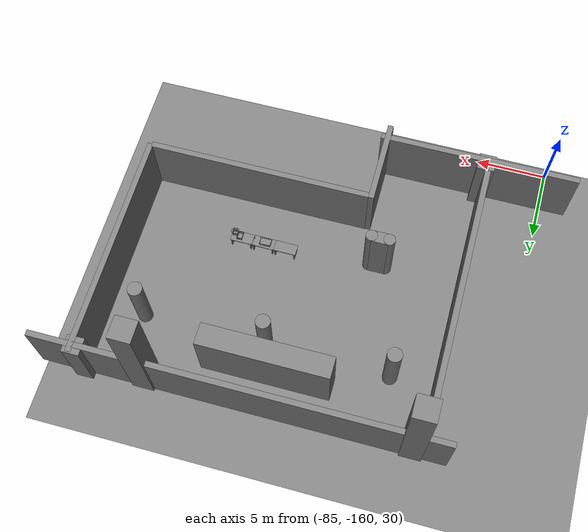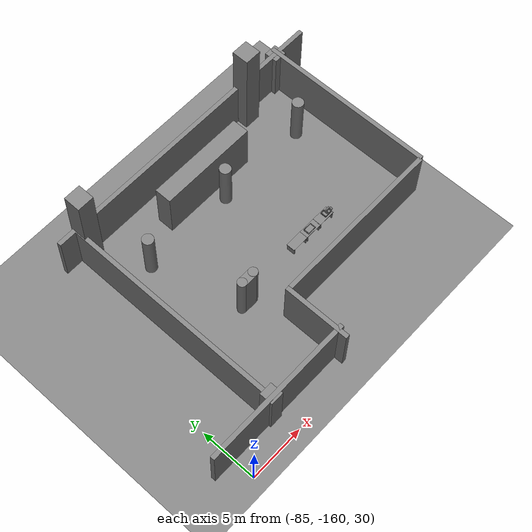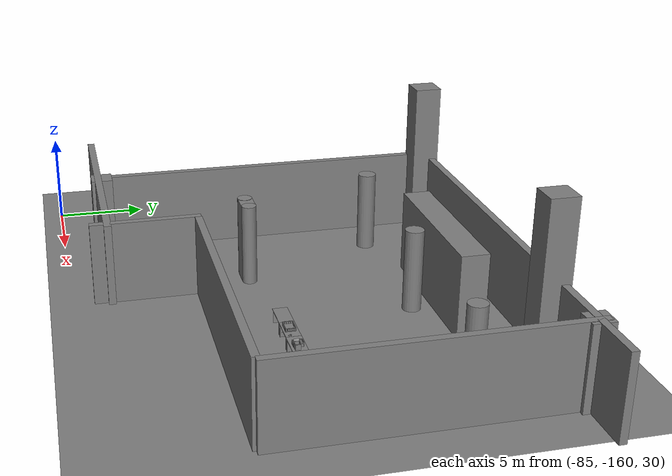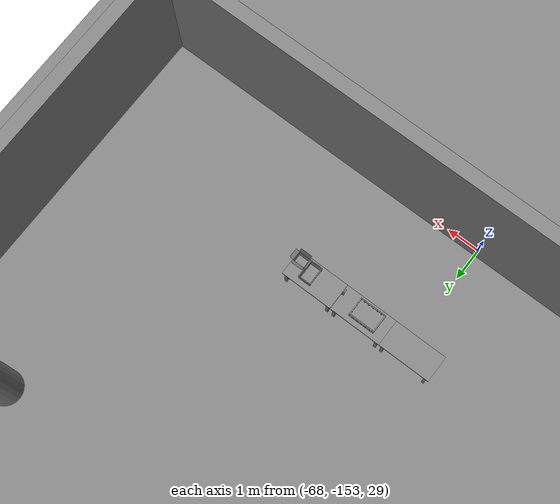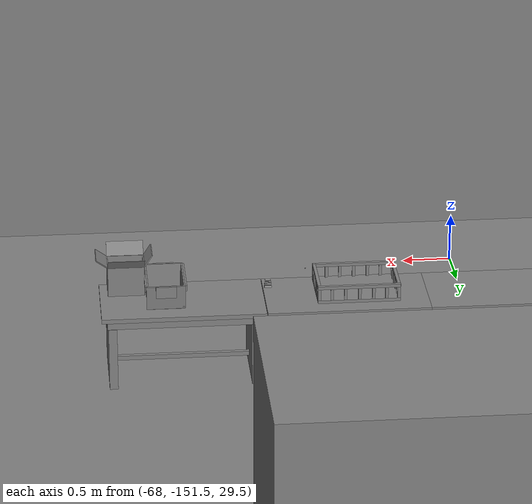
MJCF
<mujoco>
    <option gravity="0.000000000 0.000000000 -9.810000420" timestep="0.0049999999" integrator="implicitfast" density="1.225" viscosity="1.8000001e-05" noslip_iterations="10" iterations="100" sdf_iterations="50">
        <flag multiccd="disable"/>
    </option>
    <size memory="1000M"/>
    <compiler coordinate="local"/>
    <worldbody>
        <light cutoff="30" pos="0 1 1" dir="0 -1 -2"/>
        <light cutoff="30" pos="0 -1 1" dir="0 1 -2"/>
        <body pos="-64.866622925 -149.383972168 30.183746338" euler="89.999992371 89.999946594 0.000000000" name="openloong_gripper_2f85_fix_base_usda_bluebox_01">
            <geom contype="1" conaffinity="1" density="1000" type="box" material="" rgba="0.500000000 0.500000000 0.500000000 1.000000000" solimp="0.899999976 0.949999988 0.001000000" friction="1.000000000 0.005000000 0.000100000" solref="0.020000000 1.000000000" margin="0" condim="3" group="0" pos="0.276596069 0.187225342 0.000061035" quat="0.707107008 0.000077501 0.707106471 0.000077456" size="0.100000001 0.057999998 0.010000000" name="openloong_gripper_2f85_fix_base_usda_geom_A93ABB5F_E37C_45C5_B03C_B4AD5EAB50BA"/>
            <geom contype="1" conaffinity="1" density="1000" type="box" material="" rgba="0.500000000 0.500000000 0.500000000 1.000000000" solimp="0.899999976 0.949999988 0.001000000" friction="1.000000000 0.005000000 0.000100000" solref="0.020000000 1.000000000" margin="0" condim="3" group="0" pos="0.000000000 0.002883911 0.000000000" quat="1.000000000 0.000000000 0.000000000 0.000000000" size="0.254000008 0.003000000 0.172000006" name="openloong_gripper_2f85_fix_base_usda_geom_6C283FCD_6EB4_487F_B293_B4CBA0ABC1AD"/>
            <geom contype="1" conaffinity="1" density="1000" type="box" material="" rgba="0.500000000 0.500000000 0.500000000 1.000000000" solimp="0.899999976 0.949999988 0.001000000" friction="1.000000000 0.005000000 0.000100000" solref="0.020000000 1.000000000" margin="0" condim="3" group="0" pos="0.000015259 0.124874115 0.173477173" quat="0.999796450 0.020176515 -0.000000015 0.000000030" size="0.259999990 0.119999997 0.007000000" name="openloong_gripper_2f85_fix_base_usda_geom_EACDB233_D314_4534_9137_177688806D85"/>
            <geom contype="1" conaffinity="1" density="1000" type="box" material="" rgba="0.500000000 0.500000000 0.500000000 1.000000000" solimp="0.899999976 0.949999988 0.001000000" friction="1.000000000 0.005000000 0.000100000" solref="0.020000000 1.000000000" margin="0" condim="3" group="0" pos="0.000015259 0.124874115 -0.173477173" quat="0.999796450 -0.020176545 -0.000000015 0.000000000" size="0.259999990 0.119999997 0.007000000" name="openloong_gripper_2f85_fix_base_usda_geom_3E12B08F_AA8E_40FF_8F7C_634C738172C5"/>
            <geom contype="1" conaffinity="1" density="1000" type="box" material="" rgba="0.500000000 0.500000000 0.500000000 1.000000000" solimp="0.899999976 0.949999988 0.001000000" friction="1.000000000 0.005000000 0.000100000" solref="0.020000000 1.000000000" margin="0" condim="3" group="0" pos="0.000015259 0.214012146 0.188980103" quat="0.999913096 0.013176724 0.000000015 0.000000000" size="0.259999990 0.029999999 0.012500000" name="openloong_gripper_2f85_fix_base_usda_geom_70BDE0AB_DEBE_4895_9950_3E71960FC1BA"/>
            <geom contype="1" conaffinity="1" density="1000" type="box" material="" rgba="0.500000000 0.500000000 0.500000000 1.000000000" solimp="0.899999976 0.949999988 0.001000000" friction="1.000000000 0.005000000 0.000100000" solref="0.020000000 1.000000000" margin="0" condim="3" group="0" pos="-0.258346558 0.125289917 0.001876831" quat="0.702796996 -0.020792052 0.710783184 0.020769238" size="0.189999998 0.119999997 0.009000000" name="openloong_gripper_2f85_fix_base_usda_geom_F6A95658_5F80_4C5B_9901_CCADE8A88F8D"/>
            <geom contype="1" conaffinity="1" density="1000" type="box" material="" rgba="0.500000000 0.500000000 0.500000000 1.000000000" solimp="0.899999976 0.949999988 0.001000000" friction="1.000000000 0.005000000 0.000100000" solref="0.020000000 1.000000000" margin="0" condim="3" group="0" pos="0.000015259 0.214012146 -0.188980103" quat="0.999913096 -0.013176769 0.000000030 0.000000015" size="0.259999990 0.029999999 0.012500000" name="openloong_gripper_2f85_fix_base_usda_geom_0EE8DAC3_6343_44E6_B17D_2C3E11A3EB59"/>
            <geom contype="1" conaffinity="1" density="1000" type="box" material="" rgba="0.500000000 0.500000000 0.500000000 1.000000000" solimp="0.899999976 0.949999988 0.001000000" friction="1.000000000 0.005000000 0.000100000" solref="0.020000000 1.000000000" margin="0" condim="3" group="0" pos="-0.276596069 0.187225342 0.000061035" quat="0.707106650 0.000077441 0.707106709 0.000077456" size="0.100000001 0.057999998 0.010000000" name="openloong_gripper_2f85_fix_base_usda_geom_3D84B6D3_6802_4344_8524_EF3AF38A330F"/>
            <geom contype="1" conaffinity="1" density="1000" type="box" material="" rgba="0.500000000 0.500000000 0.500000000 1.000000000" solimp="0.899999976 0.949999988 0.001000000" friction="1.000000000 0.005000000 0.000100000" solref="0.020000000 1.000000000" margin="0" condim="3" group="0" pos="0.258346558 0.125289917 0.001876831" quat="0.702851534 0.018856451 0.710823834 -0.019329429" size="0.189999998 0.119999997 0.009000000" name="openloong_gripper_2f85_fix_base_usda_geom_AB42AA1C_6546_4A19_8EAD_CDDA471FAA5B"/>
            <freejoint name="openloong_gripper_2f85_fix_base_usda_bluebox_01_joint"/>
            <site size="0.005000000 0.005000000 0.005000000" rgba="0.500000000 0.500000000 0.500000000 1.000000000" pos="0.000000000 0.000000000 0.000000000" quat="0.999961913 0.008726534 0.000000000 0.000000000" group="0" type="sphere" name="openloong_gripper_2f85_fix_base_usda_bluebox_01site"/>
        </body>
        <body pos="-64.496299744 -149.491867065 30.235729218" euler="0.000000000 0.000000000 89.999946594" name="openloong_gripper_2f85_fix_base_usda_cardboardbox_01">
            <geom contype="1" conaffinity="1" density="1000" type="box" material="" rgba="0.500000000 0.500000000 0.500000000 1.000000000" solimp="0.899999976 0.949999988 0.001000000" friction="1.000000000 0.005000000 0.000100000" solref="0.020000000 1.000000000" margin="0" condim="3" group="0" pos="-0.003166199 -0.004086494 0.005052090" quat="1.000000000 0.000000000 0.000000000 0.000000000" size="0.142499998 0.177500010 0.005000000" name="openloong_gripper_2f85_fix_base_usda_geom_E96576EE_2C09_401F_A5AD_9E9D24FC7AD8"/>
            <geom contype="1" conaffinity="1" density="1000" type="box" material="" rgba="0.500000000 0.500000000 0.500000000 1.000000000" solimp="0.899999976 0.949999988 0.001000000" friction="1.000000000 0.005000000 0.000100000" solref="0.020000000 1.000000000" margin="0" condim="3" group="0" pos="-0.003166199 0.170316696 0.150570869" quat="1.000000000 0.000000000 0.000000000 0.000000000" size="0.142499998 0.005000000 0.149999991" name="openloong_gripper_2f85_fix_base_usda_geom_C93F6F2E_A49A_4BCC_804A_2CEE52170D60"/>
            <geom contype="1" conaffinity="1" density="1000" type="box" material="" rgba="0.500000000 0.500000000 0.500000000 1.000000000" solimp="0.899999976 0.949999988 0.001000000" friction="1.000000000 0.005000000 0.000100000" solref="0.020000000 1.000000000" margin="0" condim="3" group="0" pos="-0.147399902 -0.005307198 0.150570869" quat="1.000000000 0.000000000 0.000000000 0.000000000" size="0.005000000 0.177500010 0.149999991" name="openloong_gripper_2f85_fix_base_usda_geom_5EF37C74_CED4_455A_92A6_ED87148B748D"/>
            <geom contype="1" conaffinity="1" density="1000" type="box" material="" rgba="0.500000000 0.500000000 0.500000000 1.000000000" solimp="0.899999976 0.949999988 0.001000000" friction="1.000000000 0.005000000 0.000100000" solref="0.020000000 1.000000000" margin="0" condim="3" group="0" pos="0.140275955 -0.005307198 0.150570869" quat="1.000000000 0.000000000 0.000000000 0.000000000" size="0.005000000 0.177500010 0.149999991" name="openloong_gripper_2f85_fix_base_usda_geom_D61E0E46_C16E_478D_BDB4_50E8CD83D155"/>
            <geom contype="1" conaffinity="1" density="1000" type="box" material="" rgba="0.500000000 0.500000000 0.500000000 1.000000000" solimp="0.899999976 0.949999988 0.001000000" friction="1.000000000 0.005000000 0.000100000" solref="0.020000000 1.000000000" margin="0" condim="3" group="0" pos="-0.003166199 -0.181550980 0.150570869" quat="1.000000000 0.000000000 0.000000000 0.000000000" size="0.142499998 0.005000000 0.149999991" name="openloong_gripper_2f85_fix_base_usda_geom_2A709F5D_53AA_4A47_85AA_12C73ACF8F44"/>
            <freejoint name="openloong_gripper_2f85_fix_base_usda_cardboardbox_01_joint"/>
            <site size="0.005000000 0.005000000 0.005000000" rgba="0.500000000 0.500000000 0.500000000 1.000000000" pos="0.000000000 0.000000000 0.000000000" quat="0.999961913 0.008726535 0.000000000 0.000000000" group="0" type="sphere" name="openloong_gripper_2f85_fix_base_usda_site_B5E7030D_0F23_4E17_9C58_94015E07E443"/>
            <body pos="0.139160156 -0.004048347 0.301930904" euler="-179.999954224 49.383502960 179.999954224" name="openloong_gripper_2f85_fix_base_usda_A1_006">
                <geom contype="1" conaffinity="1" density="1000" type="box" material="" rgba="0.500000000 0.500000000 0.500000000 1.000000000" solimp="0.899999976 0.949999988 0.001000000" friction="1.000000000 0.005000000 0.000100000" solref="0.020000000 1.000000000" margin="0" condim="3" group="0" pos="-0.071587563 0.000009537 0.001745224" quat="0.999999881 0.000000000 0.000000000 0.000000000" size="0.071249999 0.179999992 0.002500000" name="openloong_gripper_2f85_fix_base_usda_geom_04CDB921_5B1E_44DF_A7B6_E6EA9338F4B1"/>
                <joint armature="0" stiffness="0.07" damping="0.0099999998" axis="0.000000 1.000000 0.000000" type="hinge" name="openloong_gripper_2f85_fix_base_usda_A1_006"/>
            </body>
            <body pos="-0.145902634 -0.004086494 0.301938057" euler="-180.000000000 -60.000011444 -180.000000000" name="openloong_gripper_2f85_fix_base_usda_A2_006">
                <geom contype="1" conaffinity="1" density="1000" type="box" material="" rgba="0.500000000 0.500000000 0.500000000 1.000000000" solimp="0.899999976 0.949999988 0.001000000" friction="1.000000000 0.005000000 0.000100000" solref="0.020000000 1.000000000" margin="0" condim="3" group="0" pos="0.071268082 0.000009537 0.002717972" quat="0.000002921 0.000000000 -0.000000030 0.999999881" size="0.071249999 0.179999992 0.002500000" name="openloong_gripper_2f85_fix_base_usda_geom_8678A1C5_7481_46B1_9C68_B07F945102D3"/>
                <joint armature="0" stiffness="0.07" damping="0.0099999998" axis="0.000000 1.000000 0.000000" type="hinge" name="openloong_gripper_2f85_fix_base_usda_A2_006"/>
            </body>
            <body pos="-0.003385544 0.175991058 0.301930904" euler="-125.858116150 -0.000004561 0.000002331" name="openloong_gripper_2f85_fix_base_usda_B2_006">
                <geom contype="1" conaffinity="1" density="1000" type="box" material="" rgba="0.500000000 0.500000000 0.500000000 1.000000000" solimp="0.899999976 0.949999988 0.001000000" friction="1.000000000 0.005000000 0.000100000" solref="0.020000000 1.000000000" margin="0" condim="3" group="0" pos="0.000009537 -0.070939064 -0.002470016" quat="0.999614120 0.027776197 -0.000000015 0.000000030" size="0.137500003 0.064999998 0.005000000" name="openloong_gripper_2f85_fix_base_usda_geom_C5BE4852_8AC5_49F0_9266_FA2CD7E1E0AE"/>
                <joint armature="0" stiffness="0.07" damping="0.0099999998" axis="1.000000 0.000000 0.000000" type="hinge" name="openloong_gripper_2f85_fix_base_usda_B2_006"/>
            </body>
            <body pos="-0.003385544 -0.184140205 0.301938057" euler="147.805557251 0.000000000 0.000000000" name="openloong_gripper_2f85_fix_base_usda_B1_006">
                <geom contype="1" conaffinity="1" density="1000" type="box" material="" rgba="0.500000000 0.500000000 0.500000000 1.000000000" solimp="0.899999976 0.949999988 0.001000000" friction="1.000000000 0.005000000 0.000100000" solref="0.020000000 1.000000000" margin="0" condim="3" group="0" pos="-0.000028610 0.070202351 -0.002703667" quat="0.999614179 -0.027776167 0.000000000 0.000000000" size="0.137500003 0.064999998 0.005000000" name="openloong_gripper_2f85_fix_base_usda_geom_D534B4DC_D4DC_4CA0_BB85_49F6E0040E3D"/>
                <joint armature="0" stiffness="0.07" damping="0.0099999998" axis="1.000000 0.000000 0.000000" type="hinge" name="openloong_gripper_2f85_fix_base_usda_B1_006"/>
            </body>
        </body>
        <body pos="-65.882858276 -149.481979370 30.229999542" euler="-64.487716675 0.000000000 0.000000000" name="openloong_gripper_2f85_fix_base_usda_Barcode">
            <geom contype="1" conaffinity="1" density="1000" type="box" material="" rgba="0.500000000 0.500000000 0.500000000 1.000000000" solimp="0.899999976 0.949999988 0.001000000" friction="1.000000000 0.005000000 0.000100000" solref="0.020000000 1.000000000" margin="0" condim="3" group="0" pos="0.000000000 0.013038635 0.001419067" quat="0.000000000 0.000000000 0.000000000 1.000000119" size="0.034000002 0.010000000 0.017999999" name="openloong_gripper_2f85_fix_base_usda_geom_21491EC1_3946_4B35_8FA7_52EDCDA21709"/>
            <geom contype="1" conaffinity="1" density="1000" type="box" material="" rgba="0.500000000 0.500000000 0.500000000 1.000000000" solimp="0.899999976 0.949999988 0.001000000" friction="1.000000000 0.005000000 0.000100000" solref="0.020000000 1.000000000" margin="0" condim="3" group="0" pos="0.000000000 -0.035301208 -0.007095337" quat="0.000000000 0.000000000 -0.043619365 0.999048233" size="0.028999999 0.010000000 0.020000000" name="openloong_gripper_2f85_fix_base_usda_geom_A185EC12_60D3_4BE9_AA41_44B7B552A221"/>
            <geom contype="1" conaffinity="1" density="1000" type="box" material="" rgba="0.500000000 0.500000000 0.500000000 1.000000000" solimp="0.899999976 0.949999988 0.001000000" friction="1.000000000 0.005000000 0.000100000" solref="0.020000000 1.000000000" margin="0" condim="3" group="0" pos="0.000000000 -0.043411255 -0.011749268" quat="0.922262907 0.386563420 0.000000000 0.000000000" size="0.026000001 0.010000000 0.020000000" name="openloong_gripper_2f85_fix_base_usda_geom_578EFD68_BFB9_463F_8C4A_6EAA9C9F0E4B"/>
            <geom contype="1" conaffinity="1" density="1000" type="box" material="" rgba="0.500000000 0.500000000 0.500000000 1.000000000" solimp="0.899999976 0.949999988 0.001000000" friction="1.000000000 0.005000000 0.000100000" solref="0.020000000 1.000000000" margin="0" condim="3" group="0" pos="0.000000000 -0.016967773 -0.031860352" quat="0.000000000 0.000000000 0.000000000 1.000000119" size="0.008000000 0.010000000 0.013000000" name="openloong_gripper_2f85_fix_base_usda_geom_74B8C177_D4D3_4758_AD08_9DD87A5E22BF"/>
            <geom contype="1" conaffinity="1" density="1000" type="box" material="" rgba="0.500000000 0.500000000 0.500000000 1.000000000" solimp="0.899999976 0.949999988 0.001000000" friction="1.000000000 0.005000000 0.000100000" solref="0.020000000 1.000000000" margin="0" condim="3" group="0" pos="0.000000000 -0.001869202 0.000312805" quat="0.953716993 0.300705761 0.000000000 0.000000000" size="0.032000002 0.010000000 0.018999999" name="openloong_gripper_2f85_fix_base_usda_geom_AB90454A_1CEE_4BE0_A4D2_B5A6E678B9D9"/>
            <geom contype="1" conaffinity="1" density="1000" type="box" material="" rgba="0.500000000 0.500000000 0.500000000 1.000000000" solimp="0.899999976 0.949999988 0.001000000" friction="1.000000000 0.005000000 0.000100000" solref="0.020000000 1.000000000" margin="0" condim="3" group="0" pos="0.000000000 -0.019531250 -0.003173828" quat="0.953716993 0.300705761 0.000000000 0.000000000" size="0.030999999 0.010000000 0.020000000" name="openloong_gripper_2f85_fix_base_usda_geom_1DB27079_F2D9_459A_A74D_C61DC3139C56"/>
            <geom contype="1" conaffinity="1" density="1000" type="box" material="" rgba="0.500000000 0.500000000 0.500000000 1.000000000" solimp="0.899999976 0.949999988 0.001000000" friction="1.000000000 0.005000000 0.000100000" solref="0.020000000 1.000000000" margin="0" condim="3" group="0" pos="0.000000000 -0.035301208 -0.007095337" quat="0.953716993 0.300705761 0.000000000 0.000000000" size="0.028999999 0.010000000 0.020000000" name="openloong_gripper_2f85_fix_base_usda_geom_B832C639_FAE6_4D62_81A7_492807F3B201"/>
            <geom contype="1" conaffinity="1" density="1000" type="box" material="" rgba="0.500000000 0.500000000 0.500000000 1.000000000" solimp="0.899999976 0.949999988 0.001000000" friction="1.000000000 0.005000000 0.000100000" solref="0.020000000 1.000000000" margin="0" condim="3" group="0" pos="0.000000000 -0.042617798 -0.071121216" quat="0.000000000 0.000000000 0.000000000 1.000000119" size="0.013000000 0.021000000 0.059999999" name="openloong_gripper_2f85_fix_base_usda_geom_6B90E252_BC9C_4F37_A84D_A6C79A7E0CE2"/>
            <freejoint name="openloong_gripper_2f85_fix_base_usda_Barcode_joint"/>
            <site size="0.005000000 0.005000000 0.005000000" rgba="0.500000000 0.500000000 0.500000000 1.000000000" pos="0.000000000 0.000000000 0.000000000" quat="1.000000000 0.000000000 0.000000000 0.000000000" group="0" type="sphere" name="openloong_gripper_2f85_fix_base_usda_Barcode_site"/>
        </body>
        <body pos="-66.745018005 -149.392349243 30.184000015" euler="0.000000000 0.000000000 89.999946594" name="[22329707569725]_Basket_01">
            <geom contype="1" conaffinity="1" density="1000" type="box" material="" rgba="0.500000000 0.500000000 0.500000000 1.000000000" solimp="0.899999976 0.949999988 0.001000000" friction="1.000000000 0.005000000 0.000100000" solref="0.020000000 1.000000000" margin="0" condim="3" group="0" pos="-0.052425385 0.389207840 0.089787483" quat="0.707107008 0.000000000 0.000000000 0.707106411" size="0.014249999 0.014249999 0.059999999" name="[22329707569725]_geom_BCF000A2_A7D1_4DD3_A2B4_487EE60FA826"/>
            <geom contype="1" conaffinity="1" density="1000" type="box" material="" rgba="0.500000000 0.500000000 0.500000000 1.000000000" solimp="0.899999976 0.949999988 0.001000000" friction="1.000000000 0.005000000 0.000100000" solref="0.020000000 1.000000000" margin="0" condim="3" group="0" pos="0.264015198 -0.133043289 0.089787483" quat="0.707107008 0.000000000 0.000000000 0.707106411" size="0.014249999 0.014249999 0.059999999" name="[22329707569725]_geom_89EAD587_83A9_4300_943F_0FC18B5BDC55"/>
            <geom contype="1" conaffinity="1" density="1000" type="box" material="" rgba="0.500000000 0.500000000 0.500000000 1.000000000" solimp="0.899999976 0.949999988 0.001000000" friction="1.000000000 0.005000000 0.000100000" solref="0.020000000 1.000000000" margin="0" condim="3" group="0" pos="-0.264015198 -0.265548706 0.089793205" quat="0.707107008 0.000000000 0.000000000 0.707106411" size="0.014249999 0.014249999 0.059999999" name="[22329707569725]_geom_3346E575_D7F2_4DE9_82E3_8A8F0411C94E"/>
            <geom contype="1" conaffinity="1" density="1000" type="box" material="" rgba="0.500000000 0.500000000 0.500000000 1.000000000" solimp="0.899999976 0.949999988 0.001000000" friction="1.000000000 0.005000000 0.000100000" solref="0.020000000 1.000000000" margin="0" condim="3" group="0" pos="-0.160263062 -0.389322281 0.089793205" quat="0.707107008 0.000000000 0.000000000 0.707106411" size="0.014249999 0.014249999 0.059999999" name="[22329707569725]_geom_A068FED2_38EB_4ADF_ADD4_7F1A63FE4CB5"/>
            <geom contype="1" conaffinity="1" density="1000" type="box" material="" rgba="0.500000000 0.500000000 0.500000000 1.000000000" solimp="0.899999976 0.949999988 0.001000000" friction="1.000000000 0.005000000 0.000100000" solref="0.020000000 1.000000000" margin="0" condim="3" group="0" pos="0.162265778 -0.389322281 0.089787483" quat="0.707107008 0.000000000 0.000000000 0.707106411" size="0.014249999 0.014249999 0.059999999" name="[22329707569725]_geom_AD04FF03_474A_4595_A293_91939B14E28A"/>
            <geom contype="1" conaffinity="1" density="1000" type="box" material="" rgba="0.500000000 0.500000000 0.500000000 1.000000000" solimp="0.899999976 0.949999988 0.001000000" friction="1.000000000 0.005000000 0.000100000" solref="0.020000000 1.000000000" margin="0" condim="3" group="0" pos="0.264015198 0.389207840 0.089787483" quat="0.707107008 0.000000000 0.000000000 0.707106411" size="0.014249999 0.014249999 0.059999999" name="[22329707569725]_geom_0D6A5765_3D15_4B72_A307_8CF41AE99DC1"/>
            <geom contype="1" conaffinity="1" density="1000" type="box" material="" rgba="0.500000000 0.500000000 0.500000000 1.000000000" solimp="0.899999976 0.949999988 0.001000000" friction="1.000000000 0.005000000 0.000100000" solref="0.020000000 1.000000000" margin="0" condim="3" group="0" pos="-0.264015198 -0.133043289 0.089793205" quat="0.707107008 0.000000000 0.000000000 0.707106411" size="0.014249999 0.014249999 0.059999999" name="[22329707569725]_geom_5AE3BBB4_B8FA_43E3_8BE1_C1584A1735BA"/>
            <geom contype="1" conaffinity="1" density="1000" type="box" material="" rgba="0.500000000 0.500000000 0.500000000 1.000000000" solimp="0.899999976 0.949999988 0.001000000" friction="1.000000000 0.005000000 0.000100000" solref="0.020000000 1.000000000" margin="0" condim="3" group="0" pos="-0.264026642 0.269256592 0.089793205" quat="0.707107008 0.000000000 0.000000000 0.707106411" size="0.014249999 0.014249999 0.059999999" name="[22329707569725]_geom_4D75F9BB_E2FB_4707_AAD7_B22467D9F36F"/>
            <geom contype="1" conaffinity="1" density="1000" type="box" material="" rgba="0.500000000 0.500000000 0.500000000 1.000000000" solimp="0.899999976 0.949999988 0.001000000" friction="1.000000000 0.005000000 0.000100000" solref="0.020000000 1.000000000" margin="0" condim="3" group="0" pos="0.054462433 0.389207840 0.089787483" quat="0.707107008 0.000000000 0.000000000 0.707106411" size="0.014249999 0.014249999 0.059999999" name="[22329707569725]_geom_272B581A_EE85_4B4D_A221_ED591A0F5D40"/>
            <geom contype="1" conaffinity="1" density="1000" type="box" material="" rgba="0.500000000 0.500000000 0.500000000 1.000000000" solimp="0.899999976 0.949999988 0.001000000" friction="1.000000000 0.005000000 0.000100000" solref="0.020000000 1.000000000" margin="0" condim="3" group="0" pos="0.054462433 -0.389322281 0.089787483" quat="0.707107008 0.000000000 0.000000000 0.707106411" size="0.014249999 0.014249999 0.059999999" name="[22329707569725]_geom_ADECC36F_6D3C_473E_B357_8F629530471D"/>
            <geom contype="1" conaffinity="1" density="1000" type="box" material="" rgba="0.500000000 0.500000000 0.500000000 1.000000000" solimp="0.899999976 0.949999988 0.001000000" friction="1.000000000 0.005000000 0.000100000" solref="0.020000000 1.000000000" margin="0" condim="3" group="0" pos="0.264015198 0.269256592 0.089793205" quat="0.707107008 0.000000000 0.000000000 0.707106411" size="0.014249999 0.014249999 0.059999999" name="[22329707569725]_geom_8469F2A8_3D52_449C_A287_B96928CE9A65"/>
            <geom contype="1" conaffinity="1" density="1000" type="box" material="" rgba="0.500000000 0.500000000 0.500000000 1.000000000" solimp="0.899999976 0.949999988 0.001000000" friction="1.000000000 0.005000000 0.000100000" solref="0.020000000 1.000000000" margin="0" condim="3" group="0" pos="0.264015198 -0.389322281 0.089787483" quat="0.707107008 0.000000000 0.000000000 0.707106411" size="0.014249999 0.014249999 0.059999999" name="[22329707569725]_geom_E816EF60_216F_4703_A683_52326D1AD495"/>
            <geom contype="1" conaffinity="1" density="1000" type="box" material="" rgba="0.500000000 0.500000000 0.500000000 1.000000000" solimp="0.899999976 0.949999988 0.001000000" friction="1.000000000 0.005000000 0.000100000" solref="0.020000000 1.000000000" margin="0" condim="3" group="0" pos="0.000000000 0.000000000 0.015998840" quat="0.707107008 0.000000000 0.000000000 0.707106411" size="0.403499991 0.279000014 0.015750000" name="[22329707569725]_geom_7357526B_8931_4EBD_9D85_65ACF469F42A"/>
            <geom contype="1" conaffinity="1" density="1000" type="box" material="" rgba="0.500000000 0.500000000 0.500000000 1.000000000" solimp="0.899999976 0.949999988 0.001000000" friction="1.000000000 0.005000000 0.000100000" solref="0.020000000 1.000000000" margin="0" condim="3" group="0" pos="0.000000000 -0.389476776 0.163619041" quat="0.707107008 0.000000000 0.000000000 0.707106411" size="0.015000000 0.277500004 0.015750000" name="[22329707569725]_geom_C64E74B6_89E7_4353_80F9_5FAAB5ACE5C9"/>
            <geom contype="1" conaffinity="1" density="1000" type="box" material="" rgba="0.500000000 0.500000000 0.500000000 1.000000000" solimp="0.899999976 0.949999988 0.001000000" friction="1.000000000 0.005000000 0.000100000" solref="0.020000000 1.000000000" margin="0" condim="3" group="0" pos="0.162265778 0.389207840 0.089787483" quat="0.707107008 0.000000000 0.000000000 0.707106411" size="0.014249999 0.014249999 0.059999999" name="[22329707569725]_geom_AE66EE27_ED9C_444E_AA9A_183BF875CDB8"/>
            <geom contype="1" conaffinity="1" density="1000" type="box" material="" rgba="0.500000000 0.500000000 0.500000000 1.000000000" solimp="0.899999976 0.949999988 0.001000000" friction="1.000000000 0.005000000 0.000100000" solref="0.020000000 1.000000000" margin="0" condim="3" group="0" pos="0.000000000 0.389471054 0.163619041" quat="0.707107008 0.000000000 0.000000000 0.707106411" size="0.015000000 0.277500004 0.015750000" name="[22329707569725]_geom_BD05F159_5A5B_45F3_9970_7DC44FDC5E88"/>
            <geom contype="1" conaffinity="1" density="1000" type="box" material="" rgba="0.500000000 0.500000000 0.500000000 1.000000000" solimp="0.899999976 0.949999988 0.001000000" friction="1.000000000 0.005000000 0.000100000" solref="0.020000000 1.000000000" margin="0" condim="3" group="0" pos="-0.263511658 0.000000000 0.163619041" quat="0.707107008 0.000000000 0.000000000 0.707106411" size="0.403499991 0.015000000 0.015750000" name="[22329707569725]_geom_06C9A7ED_B646_4A17_B809_E9F9D8A302ED"/>
            <geom contype="1" conaffinity="1" density="1000" type="box" material="" rgba="0.500000000 0.500000000 0.500000000 1.000000000" solimp="0.899999976 0.949999988 0.001000000" friction="1.000000000 0.005000000 0.000100000" solref="0.020000000 1.000000000" margin="0" condim="3" group="0" pos="-0.264015198 0.141334534 0.089793205" quat="0.707107008 0.000000000 0.000000000 0.707106411" size="0.014249999 0.014249999 0.059999999" name="[22329707569725]_geom_F5F4971D_011B_4392_AAEE_85D4ED53E60F"/>
            <geom contype="1" conaffinity="1" density="1000" type="box" material="" rgba="0.500000000 0.500000000 0.500000000 1.000000000" solimp="0.899999976 0.949999988 0.001000000" friction="1.000000000 0.005000000 0.000100000" solref="0.020000000 1.000000000" margin="0" condim="3" group="0" pos="0.264015198 -0.265548706 0.089787483" quat="0.707107008 0.000000000 0.000000000 0.707106411" size="0.014249999 0.014249999 0.059999999" name="[22329707569725]_geom_646DB132_3760_485E_B4B7_D7F91747D25F"/>
            <geom contype="1" conaffinity="1" density="1000" type="box" material="" rgba="0.500000000 0.500000000 0.500000000 1.000000000" solimp="0.899999976 0.949999988 0.001000000" friction="1.000000000 0.005000000 0.000100000" solref="0.020000000 1.000000000" margin="0" condim="3" group="0" pos="-0.160263062 0.389207840 0.089787483" quat="0.707107008 0.000000000 0.000000000 0.707106411" size="0.014249999 0.014249999 0.059999999" name="[22329707569725]_geom_8D1817B6_6055_4E8C_A224_AFB4E34D5110"/>
            <geom contype="1" conaffinity="1" density="1000" type="box" material="" rgba="0.500000000 0.500000000 0.500000000 1.000000000" solimp="0.899999976 0.949999988 0.001000000" friction="1.000000000 0.005000000 0.000100000" solref="0.020000000 1.000000000" margin="0" condim="3" group="0" pos="-0.052425385 -0.389322281 0.089787483" quat="0.707107008 0.000000000 0.000000000 0.707106411" size="0.014249999 0.014249999 0.059999999" name="[22329707569725]_geom_F1ED02CD_8BE8_4DAF_9D2D_4A0A0D61581A"/>
            <geom contype="1" conaffinity="1" density="1000" type="box" material="" rgba="0.500000000 0.500000000 0.500000000 1.000000000" solimp="0.899999976 0.949999988 0.001000000" friction="1.000000000 0.005000000 0.000100000" solref="0.020000000 1.000000000" margin="0" condim="3" group="0" pos="-0.264026642 -0.389322281 0.089793205" quat="0.707107008 0.000000000 0.000000000 0.707106411" size="0.014249999 0.014249999 0.059999999" name="[22329707569725]_geom_283AB590_2DB1_4C60_898D_B7AFF5ECEF3D"/>
            <geom contype="1" conaffinity="1" density="1000" type="box" material="" rgba="0.500000000 0.500000000 0.500000000 1.000000000" solimp="0.899999976 0.949999988 0.001000000" friction="1.000000000 0.005000000 0.000100000" solref="0.020000000 1.000000000" margin="0" condim="3" group="0" pos="0.264015198 0.141334534 0.089787483" quat="0.707107008 0.000000000 0.000000000 0.707106411" size="0.014249999 0.014249999 0.059999999" name="[22329707569725]_geom_71AE6744_2B57_4E97_AE1F_6D5638B2F609"/>
            <geom contype="1" conaffinity="1" density="1000" type="box" material="" rgba="0.500000000 0.500000000 0.500000000 1.000000000" solimp="0.899999976 0.949999988 0.001000000" friction="1.000000000 0.005000000 0.000100000" solref="0.020000000 1.000000000" margin="0" condim="3" group="0" pos="-0.264015198 0.389207840 0.089793205" quat="0.707107008 0.000000000 0.000000000 0.707106411" size="0.014249999 0.014249999 0.059999999" name="[22329707569725]_geom_8F93904B_3486_4636_A79C_D2FAD7F03BB4"/>
            <geom contype="1" conaffinity="1" density="1000" type="box" material="" rgba="0.500000000 0.500000000 0.500000000 1.000000000" solimp="0.899999976 0.949999988 0.001000000" friction="1.000000000 0.005000000 0.000100000" solref="0.020000000 1.000000000" margin="0" condim="3" group="0" pos="0.264015198 0.004480362 0.089787483" quat="0.707107008 0.000000000 0.000000000 0.707106411" size="0.014249999 0.014249999 0.059999999" name="[22329707569725]_geom_AEEBFD20_71AE_4356_87C2_A4ADFA09DCA3"/>
            <geom contype="1" conaffinity="1" density="1000" type="box" material="" rgba="0.500000000 0.500000000 0.500000000 1.000000000" solimp="0.899999976 0.949999988 0.001000000" friction="1.000000000 0.005000000 0.000100000" solref="0.020000000 1.000000000" margin="0" condim="3" group="0" pos="0.263694763 -0.000011444 0.163619041" quat="0.707107008 0.000000000 0.000000000 0.707106411" size="0.403499991 0.015000000 0.015750000" name="[22329707569725]_geom_78AD75B1_7B11_4909_9099_C631A2D8AE2E"/>
            <geom contype="1" conaffinity="1" density="1000" type="box" material="" rgba="0.500000000 0.500000000 0.500000000 1.000000000" solimp="0.899999976 0.949999988 0.001000000" friction="1.000000000 0.005000000 0.000100000" solref="0.020000000 1.000000000" margin="0" condim="3" group="0" pos="-0.264015198 0.004480362 0.089793205" quat="0.707107008 0.000000000 0.000000000 0.707106411" size="0.014249999 0.014249999 0.059999999" name="[22329707569725]_geom_0D91899E_2B12_468A_96CD_6884A5A00EB8"/>
            <freejoint name="[22329707569725]_joint_A79B21A8_01A6_494D_8129_A375EFC527C1"/>
        </body>
        <body pos="0.000000000 0.000000000 0.000000000" euler="0.000000000 0.000000000 0.000000000" name="Static Objects_Static Objects">
            <geom contype="1" conaffinity="1" density="1000" type="box" material="" rgba="0.500000000 0.500000000 0.500000000 1.000000000" solimp="0.899999976 0.949999988 0.001000000" friction="1.000000000 0.005000000 0.000100000" solref="0.020000000 1.000000000" margin="0" condim="3" group="0" pos="-67.544113159 -149.365814209 29.727830887" quat="0.500000417 0.499999970 0.499999553 0.499999970" size="0.381000012 0.319999993 0.041000001" name="Static Objects_geom_AD1F26EE_8950_4CA6_83BA_074BF48B0CA7"/>
            <geom contype="1" conaffinity="1" density="1000" type="box" material="" rgba="0.500000000 0.500000000 0.500000000 1.000000000" solimp="0.899999976 0.949999988 0.001000000" friction="1.000000000 0.005000000 0.000100000" solref="0.020000000 1.000000000" margin="0" condim="3" group="0" pos="-68.239501953 -149.365814209 30.086868286" quat="0.500000417 0.499999970 0.499999553 0.499999970" size="0.370999992 0.039500002 0.745000005" name="Static Objects_geom_6EAFF126_C26E_4986_A6F9_E640AA7B4648"/>
            <geom contype="1" conaffinity="1" density="1000" type="box" material="" rgba="0.500000000 0.500000000 0.500000000 1.000000000" solimp="0.899999976 0.949999988 0.001000000" friction="1.000000000 0.005000000 0.000100000" solref="0.020000000 1.000000000" margin="0" condim="3" group="0" pos="-68.239501953 -149.365814209 30.147235870" quat="0.500000417 0.499999970 0.499999553 0.499999970" size="0.400000006 0.022000000 0.800000012" name="Static Objects_geom_B9296ED0_A9B7_4877_8443_1C470CECC49D"/>
            <geom contype="1" conaffinity="1" density="1000" type="box" material="" rgba="0.500000000 0.500000000 0.500000000 1.000000000" solimp="0.899999976 0.949999988 0.001000000" friction="1.000000000 0.005000000 0.000100000" solref="0.020000000 1.000000000" margin="0" condim="3" group="0" pos="-68.934890747 -149.365814209 29.727830887" quat="0.500000417 0.499999970 0.499999553 0.499999970" size="0.381000012 0.319999993 0.041000001" name="Static Objects_geom_502067D9_6EBC_45E2_93B4_46E4C593D86F"/>
            <geom contype="1" conaffinity="1" density="1000" type="box" material="" rgba="0.500000000 0.500000000 0.500000000 1.000000000" solimp="0.899999976 0.949999988 0.001000000" friction="1.000000000 0.005000000 0.000100000" solref="0.020000000 1.000000000" margin="0" condim="3" group="0" pos="-68.239501953 -149.365814209 29.561563492" quat="0.500000417 0.499999970 0.499999553 0.499999970" size="0.020000000 0.022000000 0.660000026" name="Static Objects_geom_5E262C8A_1C48_4B89_A50F_B34EC4B4D263"/>
            <geom contype="1" conaffinity="1" density="1000" type="box" material="" rgba="0.500000000 0.500000000 0.500000000 1.000000000" solimp="0.899999976 0.949999988 0.001000000" friction="1.000000000 0.005000000 0.000100000" solref="0.020000000 1.000000000" margin="0" condim="3" group="0" pos="-65.945671082 -149.365814209 29.727830887" quat="0.500000417 0.499999970 0.499999553 0.499999970" size="0.381000012 0.319999993 0.041000001" name="Static Objects_geom_2E837B94_9E90_4C1B_8735_9CF81BECB71E"/>
            <geom contype="1" conaffinity="1" density="1000" type="box" material="" rgba="0.500000000 0.500000000 0.500000000 1.000000000" solimp="0.899999976 0.949999988 0.001000000" friction="1.000000000 0.005000000 0.000100000" solref="0.020000000 1.000000000" margin="0" condim="3" group="0" pos="-66.641059875 -149.365814209 30.086868286" quat="0.500000417 0.499999970 0.499999553 0.499999970" size="0.370999992 0.039500002 0.745000005" name="Static Objects_geom_55B4E9D0_B41A_49BB_BA31_E54207AC35B5"/>
            <geom contype="1" conaffinity="1" density="1000" type="box" material="" rgba="0.500000000 0.500000000 0.500000000 1.000000000" solimp="0.899999976 0.949999988 0.001000000" friction="1.000000000 0.005000000 0.000100000" solref="0.020000000 1.000000000" margin="0" condim="3" group="0" pos="-66.641059875 -149.365814209 30.147235870" quat="0.500000417 0.499999970 0.499999553 0.499999970" size="0.400000006 0.022000000 0.800000012" name="Static Objects_geom_55410AA5_8546_4818_A4F1_0D6D78786C1B"/>
            <geom contype="1" conaffinity="1" density="1000" type="box" material="" rgba="0.500000000 0.500000000 0.500000000 1.000000000" solimp="0.899999976 0.949999988 0.001000000" friction="1.000000000 0.005000000 0.000100000" solref="0.020000000 1.000000000" margin="0" condim="3" group="0" pos="-67.336448669 -149.365814209 29.727830887" quat="0.500000417 0.499999970 0.499999553 0.499999970" size="0.381000012 0.319999993 0.041000001" name="Static Objects_geom_CD56A957_7DEE_429D_839B_718D8CD2287C"/>
            <geom contype="1" conaffinity="1" density="1000" type="box" material="" rgba="0.500000000 0.500000000 0.500000000 1.000000000" solimp="0.899999976 0.949999988 0.001000000" friction="1.000000000 0.005000000 0.000100000" solref="0.020000000 1.000000000" margin="0" condim="3" group="0" pos="-66.641059875 -149.365814209 29.561563492" quat="0.500000417 0.499999970 0.499999553 0.499999970" size="0.020000000 0.022000000 0.660000026" name="Static Objects_geom_5B99DE02_2D0E_46BF_B923_A45F715B2AD5"/>
            <geom contype="1" conaffinity="1" density="1000" type="box" material="" rgba="0.500000000 0.500000000 0.500000000 1.000000000" solimp="0.899999976 0.949999988 0.001000000" friction="1.000000000 0.005000000 0.000100000" solref="0.020000000 1.000000000" margin="0" condim="3" group="0" pos="-64.338577271 -149.365814209 29.727830887" quat="0.500000417 0.499999970 0.499999553 0.499999970" size="0.381000012 0.319999993 0.041000001" name="Static Objects_geom_2CDED2A4_5CE0_48E6_B5C3_47B9D27E36C8"/>
            <geom contype="1" conaffinity="1" density="1000" type="box" material="" rgba="0.500000000 0.500000000 0.500000000 1.000000000" solimp="0.899999976 0.949999988 0.001000000" friction="1.000000000 0.005000000 0.000100000" solref="0.020000000 1.000000000" margin="0" condim="3" group="0" pos="-65.033966064 -149.365814209 30.086868286" quat="0.500000417 0.499999970 0.499999553 0.499999970" size="0.370999992 0.039500002 0.745000005" name="Static Objects_geom_B1D75400_9209_43BA_9EBF_4C87EE4F5FB5"/>
            <geom contype="1" conaffinity="1" density="1000" type="box" material="" rgba="0.500000000 0.500000000 0.500000000 1.000000000" solimp="0.899999976 0.949999988 0.001000000" friction="1.000000000 0.005000000 0.000100000" solref="0.020000000 1.000000000" margin="0" condim="3" group="0" pos="-65.033966064 -149.365814209 30.147235870" quat="0.500000417 0.499999970 0.499999553 0.499999970" size="0.400000006 0.022000000 0.800000012" name="Static Objects_geom_B96D43B2_4EC5_4F6B_A3A5_A32028185859"/>
            <geom contype="1" conaffinity="1" density="1000" type="box" material="" rgba="0.500000000 0.500000000 0.500000000 1.000000000" solimp="0.899999976 0.949999988 0.001000000" friction="1.000000000 0.005000000 0.000100000" solref="0.020000000 1.000000000" margin="0" condim="3" group="0" pos="-65.729354858 -149.365814209 29.727830887" quat="0.500000417 0.499999970 0.499999553 0.499999970" size="0.381000012 0.319999993 0.041000001" name="Static Objects_geom_6ABB1ECB_526E_4189_AF83_6C7546229F00"/>
            <geom contype="1" conaffinity="1" density="1000" type="box" material="" rgba="0.500000000 0.500000000 0.500000000 1.000000000" solimp="0.899999976 0.949999988 0.001000000" friction="1.000000000 0.005000000 0.000100000" solref="0.020000000 1.000000000" margin="0" condim="3" group="0" pos="-65.033966064 -149.365814209 29.561563492" quat="0.500000417 0.499999970 0.499999553 0.499999970" size="0.020000000 0.022000000 0.660000026" name="Static Objects_geom_E8F80490_590A_4948_A1AB_118B96A02678"/>
            <geom contype="1" conaffinity="1" density="1000" type="box" material="" rgba="0.500000000 0.500000000 0.500000000 1.000000000" solimp="0.899999976 0.949999988 0.001000000" friction="1.000000000 0.005000000 0.000100000" solref="0.020000000 1.000000000" margin="0" condim="3" group="0" pos="-61.754566193 -137.853729248 33.906845093" quat="0.707107067 0.000000000 0.000000000 0.707106471" size="0.759999990 0.759999990 4.500000000" name="Static Objects_geom_3E39513E_0050_47CA_BD5F_49EBD2C12B1A"/>
            <geom contype="1" conaffinity="1" density="1000" type="box" material="" rgba="0.500000000 0.500000000 0.500000000 1.000000000" solimp="0.899999976 0.949999988 0.001000000" friction="1.000000000 0.005000000 0.000100000" solref="0.020000000 1.000000000" margin="0" condim="3" group="0" pos="-57.511135101 -144.927108765 31.707921982" quat="1.000000000 0.000000000 0.000000000 0.000000000" size="0.200000003 8.000000000 2.299999952" name="Static Objects_geom_423B5E21_0745_4C5B_A89E_A0D2FB8A454A"/>
            <geom contype="1" conaffinity="1" density="1000" type="box" material="" rgba="0.500000000 0.500000000 0.500000000 1.000000000" solimp="0.899999976 0.949999988 0.001000000" friction="1.000000000 0.005000000 0.000100000" solref="0.020000000 1.000000000" margin="0" condim="3" group="0" pos="-80.517646790 -157.574050903 31.688196182" quat="0.707107067 0.000000000 0.000000000 0.707106471" size="0.600000024 0.600000024 2.299999952" name="Static Objects_geom_F92BCCD1_72BA_415C_A655_A995BEEBB63B"/>
            <geom contype="1" conaffinity="1" density="1000" type="box" material="" rgba="0.500000000 0.500000000 0.500000000 1.000000000" solimp="0.899999976 0.949999988 0.001000000" friction="1.000000000 0.005000000 0.000100000" solref="0.020000000 1.000000000" margin="0" condim="3" group="0" pos="-80.711044312 -147.414932251 31.666158676" quat="1.000000000 0.000000000 0.000000000 0.000000000" size="0.200000003 10.000000000 2.299999952" name="Static Objects_geom_EA7CFBD9_2DFD_4131_A032_38A3BC9629A2"/>
            <geom contype="1" conaffinity="1" density="1000" type="box" material="" rgba="0.500000000 0.500000000 0.500000000 1.000000000" solimp="0.899999976 0.949999988 0.001000000" friction="1.000000000 0.005000000 0.000100000" solref="0.020000000 1.000000000" margin="0" condim="3" group="0" pos="-57.687217712 -137.434692383 31.688196182" quat="0.707107067 0.000000000 0.000000000 0.707106471" size="0.600000024 0.600000024 2.299999952" name="Static Objects_geom_81A42DAA_6317_4367_A51C_4A5C65BEBD4A"/>
            <geom contype="1" conaffinity="1" density="1000" type="box" material="" rgba="0.500000000 0.500000000 0.500000000 1.000000000" solimp="0.899999976 0.949999988 0.001000000" friction="1.000000000 0.005000000 0.000100000" solref="0.020000000 1.000000000" margin="0" condim="3" group="0" pos="-69.537033081 -140.263229370 31.714921951" quat="0.707107067 0.000000000 0.000000000 0.707106471" size="0.759999990 4.500000000 2.299999952" name="Static Objects_geom_55D00124_4D0D_4AA4_8D25_81D609D88B5F"/>
            <geom contype="1" conaffinity="1" density="1000" type="box" material="" rgba="0.500000000 0.500000000 0.500000000 1.000000000" solimp="0.899999976 0.949999988 0.001000000" friction="1.000000000 0.005000000 0.000100000" solref="0.020000000 1.000000000" margin="0" condim="3" group="0" pos="-80.073638916 -137.853713989 33.906845093" quat="0.707107067 0.000000000 0.000000000 0.707106471" size="0.759999990 0.759999990 4.500000000" name="Static Objects_geom_DADA8C38_1B3D_4F09_84D6_84E77EECA184"/>
            <geom contype="1" conaffinity="1" density="1000" type="box" material="" rgba="0.500000000 0.500000000 0.500000000 1.000000000" solimp="0.899999976 0.949999988 0.001000000" friction="1.000000000 0.005000000 0.000100000" solref="0.020000000 1.000000000" margin="0" condim="3" group="0" pos="-73.406707764 -155.734664917 31.707921982" quat="1.000000000 0.000000000 0.000000000 0.000000000" size="0.200000003 3.000000000 2.299999952" name="Static Objects_geom_01248066_DE23_47F0_AB12_09C58D9851CD"/>
            <geom contype="1" conaffinity="1" density="1000" type="box" material="" rgba="0.500000000 0.500000000 0.500000000 1.000000000" solimp="0.899999976 0.949999988 0.001000000" friction="1.000000000 0.005000000 0.000100000" solref="0.020000000 1.000000000" margin="0" condim="3" group="0" pos="-68.497543335 -137.448257446 31.707921982" quat="0.707107067 0.000000000 0.000000000 0.707106471" size="0.200000003 14.000000000 2.299999952" name="Static Objects_geom_B3F631D9_3EA3_4C91_AD40_2575FC3EAF80"/>
            <geom contype="1" conaffinity="1" density="1000" type="cylinder" material="" rgba="0.500000000 0.500000000 0.500000000 1.000000000" solimp="0.899999976 0.949999988 0.001000000" friction="1.000000000 0.005000000 0.000100000" solref="0.020000000 1.000000000" margin="0" condim="3" group="0" pos="-68.868522644 -142.134506226 31.711090088" quat="0.707107067 0.000000000 0.000000000 0.707106471" size="0.509999990 2.299999952 1.000000000" name="Static Objects_geom_923C2972_B0A7_453C_BED0_6671FE202D51"/>
            <geom contype="1" conaffinity="1" density="1000" type="plane" material="" rgba="0.500000000 0.500000000 0.500000000 1.000000000" solimp="0.899999976 0.949999988 0.001000000" friction="1.000000000 0.005000000 0.000100000" solref="0.020000000 1.000000000" margin="0" condim="3" group="0" pos="-72.873703003 -147.131927490 29.409669876" quat="1.000000000 0.000000000 0.000000000 0.000000000" size="18.000000000 14.000000000 1.000000000" name="Static Objects_geom_8B67E819_364B_4582_84D5_BDA4DCCF59E3"/>
            <geom contype="1" conaffinity="1" density="1000" type="box" material="" rgba="0.500000000 0.500000000 0.500000000 1.000000000" solimp="0.899999976 0.949999988 0.001000000" friction="1.000000000 0.005000000 0.000100000" solref="0.020000000 1.000000000" margin="0" condim="3" group="0" pos="-79.943580627 -157.782272339 31.707921982" quat="0.707107067 0.000000000 0.000000000 0.707106471" size="0.200000003 7.000000000 2.299999952" name="Static Objects_geom_6EA80978_A21E_4C46_A0A0_221D68BE7CEB"/>
            <geom contype="1" conaffinity="1" density="1000" type="box" material="" rgba="0.500000000 0.500000000 0.500000000 1.000000000" solimp="0.899999976 0.949999988 0.001000000" friction="1.000000000 0.005000000 0.000100000" solref="0.020000000 1.000000000" margin="0" condim="3" group="0" pos="-65.421028137 -152.903442383 31.707921982" quat="0.707107067 0.000000000 0.000000000 0.707106471" size="0.200000003 7.800000191 2.299999952" name="Static Objects_geom_90CA0430_929A_4A58_85C9_B800BE852046"/>
            <geom contype="1" conaffinity="1" density="1000" type="box" material="" rgba="0.500000000 0.500000000 0.500000000 1.000000000" solimp="0.899999976 0.949999988 0.001000000" friction="1.000000000 0.005000000 0.000100000" solref="0.020000000 1.000000000" margin="0" condim="3" group="0" pos="-74.776908875 -149.964416504 31.688196182" quat="1.000000000 0.000000000 0.000000000 0.000000000" size="0.600000024 0.409999996 2.299999952" name="Static Objects_geom_AAB2F744_28F8_4679_BFFF_183D4D544919"/>
            <geom contype="1" conaffinity="1" density="1000" type="cylinder" material="" rgba="0.500000000 0.500000000 0.500000000 1.000000000" solimp="0.899999976 0.949999988 0.001000000" friction="1.000000000 0.005000000 0.000100000" solref="0.020000000 1.000000000" margin="0" condim="3" group="0" pos="-60.161884308 -142.134506226 31.711090088" quat="0.707107067 0.000000000 0.000000000 0.707106471" size="0.509999990 2.299999952 1.000000000" name="Static Objects_geom_36C0B618_96F2_4271_BCEB_064AB4A12053"/>
            <geom contype="1" conaffinity="1" density="1000" type="cylinder" material="" rgba="0.500000000 0.500000000 0.500000000 1.000000000" solimp="0.899999976 0.949999988 0.001000000" friction="1.000000000 0.005000000 0.000100000" solref="0.020000000 1.000000000" margin="0" condim="3" group="0" pos="-75.382453918 -149.963455200 31.711090088" quat="0.707107067 0.000000000 0.000000000 0.707106471" size="0.409999996 2.299999952 1.000000000" name="Static Objects_geom_6CF6AB8F_7006_440F_B468_D0BEF8D4427E"/>
            <geom contype="1" conaffinity="1" density="1000" type="cylinder" material="" rgba="0.500000000 0.500000000 0.500000000 1.000000000" solimp="0.899999976 0.949999988 0.001000000" friction="1.000000000 0.005000000 0.000100000" solref="0.020000000 1.000000000" margin="0" condim="3" group="0" pos="-74.154960632 -149.963455200 31.711090088" quat="0.707107067 0.000000000 0.000000000 0.707106471" size="0.409999996 2.299999952 1.000000000" name="Static Objects_geom_01D83B36_A269_47DE_99A8_D70BFB1F2369"/>
            <geom contype="1" conaffinity="1" density="1000" type="cylinder" material="" rgba="0.500000000 0.500000000 0.500000000 1.000000000" solimp="0.899999976 0.949999988 0.001000000" friction="1.000000000 0.005000000 0.000100000" solref="0.020000000 1.000000000" margin="0" condim="3" group="0" pos="-77.566612244 -142.134506226 31.711090088" quat="0.707107067 0.000000000 0.000000000 0.707106471" size="0.509999990 2.299999952 1.000000000" name="Static Objects_geom_34308642_A6C7_4B72_8DC7_233FFDF93483"/>
        </body>
        <body pos="-66.291030884 -149.869689941 29.018842697" euler="0.000000000 0.000000000 89.999946594" mocap="true" name="openloong_gripper_2f85_fix_base_usda_leftHandMocap"/>
        <body pos="-66.291030884 -149.869689941 29.018842697" euler="0.000000000 0.000000000 89.999946594" mocap="true" name="openloong_gripper_2f85_fix_base_usda_rightHandMocap"/>
        <body pos="-66.291030884 -149.869689941 30.218843460" euler="0.000000000 0.000000000 89.999946594" name="openloong_gripper_2f85_fix_base_usda_base_link">
            <geom contype="1" conaffinity="1" density="1000" type="mesh" material="" rgba="0.783999979 0.783999979 0.783999979 1.000000000" solimp="0.899999976 0.949999988 0.001000000" friction="1.000000000 0.005000000 0.000100000" solref="0.020000000 1.000000000" margin="0" condim="3" group="3" mesh="base_link" pos="0.000000000 0.000000000 0.000000000" quat="1.000000000 0.000000000 0.000000000 0.000000000" size="1.000000000 1.000000000 1.000000000" name="openloong_gripper_2f85_fix_base_usda__geom_7_CC51E35F_4022_4F48_B016_5F7291386837"/>
            <site size="0.005000000 0.005000000 0.005000000" rgba="0.500000000 0.500000000 0.500000000 1.000000000" pos="0.000000000 0.000000000 0.000000000" quat="1.000000000 0.000000000 0.000000000 0.000000000" group="0" type="sphere" name="openloong_gripper_2f85_fix_base_usda_imu"/>
            <inertial mass="22.447001" pos="-0.005664100 -0.001336700 0.238289997" diaginertia="0.374352545 0.277180195 0.220617250" quat="0.999247074 0.035235517 -0.015086859 0.006023135"/>
            <body pos="0.000000000 0.000000000 0.299997330" euler="0.000000000 0.000000000 0.000000000" name="openloong_gripper_2f85_fix_base_usda_dummy_body">
                <geom contype="1" conaffinity="1" density="1000" type="sphere" material="" rgba="0.783999979 0.783999979 0.783999979 1.000000000" solimp="0.899999976 0.949999988 0.001000000" friction="1.000000000 0.005000000 0.000100000" solref="0.020000000 1.000000000" margin="0" condim="3" group="3" pos="0.000000000 0.000000000 0.000000000" quat="1.000000000 0.000000000 0.000000000 0.000000000" size="0.010000000 0.000000000 0.000000000" name="openloong_gripper_2f85_fix_base_usda__geom_8_2D6B2272_96F3_472E_B9BC_F7FAA9DBCAB7"/>
                <joint armature="0.0099999998" stiffness="0" damping="0.1" axis="0.000000 0.000000 1.000000" type="hinge" name="openloong_gripper_2f85_fix_base_usda_dummy_joint"/>
                <site size="0.010000000 0.005000000 0.005000000" rgba="0.500000000 0.500000000 0.500000000 1.000000000" pos="0.000000000 0.000000000 0.000000000" quat="1.000000000 0.000000000 0.000000000 0.000000000" group="3" type="sphere" name="openloong_gripper_2f85_fix_base_usda_dummy_site"/>
            </body>
            <body pos="0.009002686 0.000000000 0.406400681" euler="0.000000000 0.000000000 0.000000000" name="openloong_gripper_2f85_fix_base_usda_Link_head_yaw">
                <geom contype="1" conaffinity="1" density="1000" type="mesh" material="" rgba="0.783999979 0.783999979 0.783999979 1.000000000" solimp="0.899999976 0.949999988 0.001000000" friction="1.000000000 0.005000000 0.000100000" solref="0.020000000 1.000000000" margin="0" condim="3" group="3" mesh="Link_head_yaw" pos="0.000000000 0.000000000 0.000000000" quat="1.000000000 0.000000000 0.000000000 0.000000000" size="1.000000000 1.000000000 1.000000000" name="openloong_gripper_2f85_fix_base_usda__geom_10_9F55E285_2212_4B35_BC24_DD1EEF0D07C4"/>
                <inertial mass="0.84249002" pos="0.000000000 -0.002081400 0.044801001" diaginertia="0.000700588 0.000629000 0.000553812" quat="0.706933022 -0.015675601 0.015677100 0.706933022"/>
                <body pos="0.000000000 -0.034599304 0.048500061" euler="0.000000000 0.000000000 0.000000000" name="openloong_gripper_2f85_fix_base_usda_Link_head_pitch">
                    <geom contype="1" conaffinity="1" density="1000" type="mesh" material="" rgba="0.783999979 0.783999979 0.783999979 1.000000000" solimp="0.899999976 0.949999988 0.001000000" friction="1.000000000 0.005000000 0.000100000" solref="0.020000000 1.000000000" margin="0" condim="3" group="3" mesh="Link_head_pitch" pos="0.000000000 0.000000000 0.000000000" quat="1.000000000 0.000000000 0.000000000 0.000000000" size="1.000000000 1.000000000 1.000000000" name="openloong_gripper_2f85_fix_base_usda__geom_12_596B19A1_666C_45DA_B6F6_43FC79E65D8D"/>
                    <inertial mass="1.3943" pos="0.020569000 0.033004001 0.125000000" diaginertia="0.006381400 0.006289940 0.004481460" quat="0.973390222 0.008406822 0.228157058 0.019624906"/>
                    <body pos="0.000000000 0.029998779 0.000000000" euler="0.000000000 0.000000000 0.000000000" name="openloong_gripper_2f85_fix_base_usda_neck_center_body">
                        <site size="0.010000000 0.005000000 0.005000000" rgba="0.500000000 0.500000000 0.500000000 1.000000000" pos="0.000000000 0.000000000 0.000000000" quat="1.000000000 0.000000000 0.000000000 0.000000000" group="3" type="sphere" name="openloong_gripper_2f85_fix_base_usda_neck_center_site"/>
                        <body pos="0.020004272 0.000000000 0.149999619" euler="-0.000002229 39.998176575 -90.000205994" name="openloong_gripper_2f85_fix_base_usda_camera_head">
                            <site size="0.010000000 0.005000000 0.005000000" rgba="0.500000000 0.500000000 0.500000000 1.000000000" pos="0.000000000 0.000000000 0.000000000" quat="1.000000000 0.000000000 0.000000000 0.000000000" group="3" type="sphere" name="openloong_gripper_2f85_fix_base_usda_camera_head_site"/>
                        </body>
                    </body>
                </body>
            </body>
            <body pos="0.003997803 -0.161598206 0.392200470" euler="0.000000000 0.000000000 0.000000000" name="openloong_gripper_2f85_fix_base_usda_Link_arm_r_01">
                <geom contype="1" conaffinity="1" density="1000" type="mesh" material="" rgba="0.783999979 0.783999979 0.783999979 1.000000000" solimp="0.899999976 0.949999988 0.001000000" friction="1.000000000 0.005000000 0.000100000" solref="0.020000000 1.000000000" margin="0" condim="3" group="3" mesh="Link_arm_r_01" pos="0.000000000 0.000000000 0.000000000" quat="1.000000000 0.000000000 0.000000000 0.000000000" size="1.000000000 1.000000000 1.000000000" name="openloong_gripper_2f85_fix_base_usda__geom_14_B8DBAD87_D000_43BD_A1D6_3D803A85BE0F"/>
                <joint armature="0.0099999998" stiffness="0" damping="1" axis="0.000000 -1.000000 0.000000" limited="true" range="-170.000015259 170.000015259" type="hinge" name="openloong_gripper_2f85_fix_base_usda_J_arm_r_01"/>
                <inertial mass="0.75641" pos="0.004494600 -0.038293999 -0.000001874" diaginertia="0.000842990 0.000803050 0.000587120" quat="-0.000163502 0.707098067 0.000812463 0.707115054"/>
                <body pos="-0.041992188 -0.041000366 0.000000000" euler="0.000000000 0.000000000 0.000000000" name="openloong_gripper_2f85_fix_base_usda_Link_arm_r_02">
                    <geom contype="1" conaffinity="1" density="1000" type="mesh" material="" rgba="0.783999979 0.783999979 0.783999979 1.000000000" solimp="0.899999976 0.949999988 0.001000000" friction="1.000000000 0.005000000 0.000100000" solref="0.020000000 1.000000000" margin="0" condim="3" group="3" mesh="Link_arm_r_02" pos="0.000000000 0.000000000 0.000000000" quat="1.000000000 0.000000000 0.000000000 0.000000000" size="1.000000000 1.000000000 1.000000000" name="openloong_gripper_2f85_fix_base_usda__geom_16_57AE8F5F_5BC8_49DD_B18C_E57FF16AB0BD"/>
                    <joint armature="0.0099999998" stiffness="0" damping="1" axis="-1.000000 0.000000 0.000000" limited="true" range="-105.000244141 105.000244141" type="hinge" name="openloong_gripper_2f85_fix_base_usda_J_arm_r_02"/>
                    <inertial mass="0.98500001" pos="0.041999999 -0.067430697 0.000000000" diaginertia="0.002262690 0.001730990 0.001154020" quat="0.500000000 0.500000000 -0.500000000 0.500000000"/>
                    <body pos="0.041992188 -0.122596741 0.000000000" euler="0.000000000 0.000000000 0.000000000" name="openloong_gripper_2f85_fix_base_usda_Link_arm_r_03">
                        <geom contype="1" conaffinity="1" density="1000" type="mesh" material="" rgba="0.783999979 0.783999979 0.783999979 1.000000000" solimp="0.899999976 0.949999988 0.001000000" friction="1.000000000 0.005000000 0.000100000" solref="0.020000000 1.000000000" margin="0" condim="3" group="3" mesh="Link_arm_r_03" pos="0.000000000 0.000000000 0.000000000" quat="1.000000000 0.000000000 0.000000000 0.000000000" size="1.000000000 1.000000000 1.000000000" name="openloong_gripper_2f85_fix_base_usda__geom_18_D26B5F50_3299_4B94_9C54_FDE50277B27C"/>
                        <joint armature="0.0099999998" stiffness="0" damping="1" axis="0.000000 -1.000000 0.000000" limited="true" range="-170.000015259 170.000015259" type="hinge" name="openloong_gripper_2f85_fix_base_usda_J_arm_r_03"/>
                        <inertial mass="0.95899999" pos="-0.001413580 -0.164663002 0.020757901" diaginertia="0.002101340 0.002064590 0.000754802" quat="0.560480952 0.454391927 -0.443732947 0.531497955"/>
                        <body pos="0.035293579 -0.177406311 0.023998260" euler="0.000000000 0.000000000 0.000000000" name="openloong_gripper_2f85_fix_base_usda_Link_arm_r_04">
                            <geom contype="1" conaffinity="1" density="1000" type="mesh" material="" rgba="0.783999979 0.783999979 0.783999979 1.000000000" solimp="0.899999976 0.949999988 0.001000000" friction="1.000000000 0.005000000 0.000100000" solref="0.020000000 1.000000000" margin="0" condim="3" group="3" mesh="Link_arm_r_04" pos="0.000000000 0.000000000 0.000000000" quat="1.000000000 0.000000000 0.000000000 0.000000000" size="1.000000000 1.000000000 1.000000000" name="openloong_gripper_2f85_fix_base_usda__geom_20_837B33A4_43DF_4F42_8909_F84791AB9382"/>
                            <joint armature="0.0099999998" stiffness="0" damping="1" axis="-1.000000 0.000000 0.000000" limited="true" range="0.000000000 170.000015259" type="hinge" name="openloong_gripper_2f85_fix_base_usda_J_arm_r_04"/>
                            <inertial mass="0.60000002" pos="-0.038727000 -0.060766999 -0.021003000" diaginertia="0.001092610 0.000712422 0.000645102" quat="0.327701002 0.632602990 -0.467366993 0.523443997"/>
                            <body pos="-0.035293579 -0.103492737 -0.023998260" euler="0.000000000 0.000000000 0.000000000" name="openloong_gripper_2f85_fix_base_usda_Link_arm_r_05">
                                <geom contype="1" conaffinity="1" density="1000" type="mesh" material="" rgba="0.783999979 0.783999979 0.783999979 1.000000000" solimp="0.899999976 0.949999988 0.001000000" friction="1.000000000 0.005000000 0.000100000" solref="0.020000000 1.000000000" margin="0" condim="3" group="3" mesh="Link_arm_r_05" pos="0.000000000 0.000000000 0.000000000" quat="1.000000000 0.000000000 0.000000000 0.000000000" size="1.000000000 1.000000000 1.000000000" name="openloong_gripper_2f85_fix_base_usda__geom_22_DAFC4D6A_100D_4350_B082_D839C742878C"/>
                                <joint armature="0.0099999998" stiffness="0" damping="1" axis="0.000000 -1.000000 0.000000" limited="true" range="-170.000015259 170.000015259" type="hinge" name="openloong_gripper_2f85_fix_base_usda_J_arm_r_05"/>
                                <inertial mass="0.68976003" pos="0.000032712 -0.068658002 -0.000111780" diaginertia="0.002522510 0.002411100 0.000448695" quat="0.707660973 0.706543028 -0.002603360 0.002470550"/>
                                <body pos="-0.026489258 -0.196502686 0.000000000" euler="0.000000000 0.000000000 0.000000000" name="openloong_gripper_2f85_fix_base_usda_Link_arm_r_06">
                                    <geom contype="1" conaffinity="1" density="1000" type="mesh" material="" rgba="0.783999979 0.783999979 0.783999979 1.000000000" solimp="0.899999976 0.949999988 0.001000000" friction="1.000000000 0.005000000 0.000100000" solref="0.020000000 1.000000000" margin="0" condim="3" group="3" mesh="Link_arm_r_06" pos="0.000000000 0.000000000 0.000000000" quat="1.000000000 0.000000000 0.000000000 0.000000000" size="1.000000000 1.000000000 1.000000000" name="openloong_gripper_2f85_fix_base_usda__geom_24_A68BE01F_0E57_4EF3_B24C_D6D05D9025FD"/>
                                    <joint armature="0.0099999998" stiffness="0" damping="1" axis="1.000000 0.000000 0.000000" limited="true" range="-105.000244141 105.000244141" type="hinge" name="openloong_gripper_2f85_fix_base_usda_J_arm_r_06"/>
                                    <inertial mass="0.28" pos="0.026078001 -0.000000896 0.001663700" diaginertia="0.000156930 0.000145601 0.000104979" quat="0.707080841 0.001851080 0.001883810 0.707127810"/>
                                    <body pos="0.026489258 0.000000000 0.031799316" euler="0.000000000 0.000000000 0.000000000" name="openloong_gripper_2f85_fix_base_usda_Link_arm_r_07">
                                        <geom contype="1" conaffinity="1" density="1000" type="mesh" material="" rgba="0.783999979 0.783999979 0.783999979 1.000000000" solimp="0.899999976 0.949999988 0.001000000" friction="1.000000000 0.005000000 0.000100000" solref="0.020000000 1.000000000" margin="0" condim="3" group="3" mesh="Link_arm_r_07" pos="0.000000000 0.000000000 0.000000000" quat="1.000000000 0.000000000 0.000000000 0.000000000" size="1.000000000 1.000000000 1.000000000" name="openloong_gripper_2f85_fix_base_usda__geom_26_3BAF6643_4D84_4714_965C_F1566BA504A3"/>
                                        <joint armature="0.0099999998" stiffness="0" damping="1" axis="0.000000 0.000000 1.000000" limited="true" range="-60.000133514 60.000133514" type="hinge" name="openloong_gripper_2f85_fix_base_usda_J_arm_r_07"/>
                                        <inertial mass="0.61353999" pos="-0.007859000 -0.158170000 -0.027736001" diaginertia="0.003037610 0.002570910 0.000729379" quat="0.427542925 0.443532884 -0.553093910 0.560867906"/>
                                        <body pos="0.000000000 0.286994934 -0.270000458" euler="150.000350952 -0.000001649 -0.000000442" name="openloong_gripper_2f85_fix_base_usda_camera_wrist_r">
                                            <site size="0.010000000 0.005000000 0.005000000" rgba="0.500000000 0.500000000 0.500000000 1.000000000" pos="0.000000000 0.000000000 0.000000000" quat="1.000000000 0.000000000 0.000000000 0.000000000" group="3" type="sphere" name="openloong_gripper_2f85_fix_base_usda_camera_wrist_r_site"/>
                                        </body>
                                        <body pos="0.000000000 -0.220008850 -0.033002853" euler="0.000000000 0.000000000 179.999969482" name="openloong_gripper_2f85_fix_base_usda_ee_center_body_r">
                                            <site size="0.010000000 0.005000000 0.005000000" rgba="0.500000000 0.500000000 0.500000000 1.000000000" pos="0.000000000 0.000000000 0.000000000" quat="1.000000000 0.000000000 0.000000000 0.000000000" group="3" type="sphere" name="openloong_gripper_2f85_fix_base_usda_ee_center_site_r"/>
                                        </body>
                                        <body pos="0.000000000 -0.066001892 -0.031000137" euler="89.999984741 0.000000000 180.000000000" name="openloong_gripper_2f85_fix_base_usda_zbr_base_link">
                                            <geom contype="1" conaffinity="1" density="1000" type="mesh" material="" rgba="0.783999979 0.783999979 0.783999979 1.000000000" solimp="0.899999976 0.949999988 0.001000000" friction="1.000000000 0.005000000 0.000100000" solref="0.020000000 1.000000000" margin="0" condim="3" group="3" mesh="base" pos="0.000000000 0.000003815 -0.000007629" quat="1.000000000 0.000000000 0.000000000 0.000000000" size="1.000000238 1.000000238 1.000000238" name="openloong_gripper_2f85_fix_base_usda__geom_30_7BA0209B_1972_4176_9AB1_EBC20498B5B8"/>
                                            <inertial mass="0.77744102" pos="0.000000000 -0.000027039 0.035467502" diaginertia="0.000260285 0.000225381 0.000152708" quat="0.999998808 -0.001528488 0.000000000 0.000000000"/>
                                            <body pos="-0.030609138 0.004745484 0.065696731" euler="-89.999984741 -0.000000000 0.000000000" name="openloong_gripper_2f85_fix_base_usda_r_left_driver">
                                                <geom contype="1" conaffinity="1" density="1000" type="mesh" material="" rgba="0.783999979 0.783999979 0.783999979 1.000000000" solimp="0.899999976 0.949999988 0.001000000" friction="1.000000000 0.005000000 0.000100000" solref="0.020000000 1.000000000" margin="0" condim="3" group="3" mesh="driver" pos="0.030609138 0.054901138 -0.004699708" quat="0.707106829 0.707106709 0.000000000 -0.000000000" size="1.000000238 1.000000238 1.000000238" name="openloong_gripper_2f85_fix_base_usda__geom_32_2BC44F2D_6F65_428D_813D_CBA9C790BF4F"/>
                                                <joint armature="0.0049999999" stiffness="0" damping="0.1" axis="0.000000 0.000000 1.000000" limited="true" range="0.000000000 51.566200256" type="hinge" name="openloong_gripper_2f85_fix_base_usda_r_left_driver_joint"/>
                                                <inertial mass="0.0089956298" pos="0.000000000 0.017754700 0.001073140" diaginertia="0.000001724 0.000001609 0.000000322" quat="0.681301236 0.732003212 0.000000000 0.000000000"/>
                                                <body pos="-0.031402595 0.004524232 -0.010200503" euler="0.000000000 0.000000000 180.000000000" name="openloong_gripper_2f85_fix_base_usda_r_left_coupler">
                                                    <geom contype="1" conaffinity="1" density="1000" type="mesh" material="" rgba="0.783999979 0.783999979 0.783999979 1.000000000" solimp="0.899999976 0.949999988 0.001000000" friction="1.000000000 0.005000000 0.000100000" solref="0.020000000 1.000000000" margin="0" condim="3" group="3" mesh="coupler" pos="-0.062011734 -0.050354015 0.005500795" quat="0.707106829 -0.707106709 0.000000000 -0.000000000" size="1.000000238 1.000000238 1.000000238" name="openloong_gripper_2f85_fix_base_usda__geom_34_86D42236_FEF3_4D40_B9EE_6A6994587C53"/>
                                                    <inertial mass="0.0140974" pos="0.000000000 0.003012090 0.023217499" diaginertia="0.000004162 0.000003522 0.000000888" quat="0.705635548 -0.045590367 0.045590367 0.705635548"/>
                                                </body>
                                            </body>
                                            <body pos="-0.012695315 -0.012001040 0.072212234" euler="-89.999984741 -0.000000000 0.000000000" name="openloong_gripper_2f85_fix_base_usda_r_left_spring_link">
                                                <geom contype="1" conaffinity="1" density="1000" type="mesh" material="" rgba="0.783999979 0.783999979 0.783999979 1.000000000" solimp="0.899999976 0.949999988 0.001000000" friction="1.000000000 0.005000000 0.000100000" solref="0.020000000 1.000000000" margin="0" condim="3" group="3" mesh="spring_link" pos="0.012695315 0.061416641 0.012050631" quat="0.707106829 0.707106709 0.000000000 -0.000000000" size="1.000000238 1.000000238 1.000000238" name="openloong_gripper_2f85_fix_base_usda__geom_36_D39B2279_8EEC_483C_94D2_6E9D0844BAEF"/>
                                                <joint armature="0.001" stiffness="0.050000001" damping="0.00125" axis="0.000000 0.000000 1.000000" limited="true" range="-17.000000000 51.566200256" type="hinge" name="openloong_gripper_2f85_fix_base_usda_r_left_spring_link_joint"/>
                                                <inertial mass="0.0221642" pos="-0.000000009 0.018162400 0.021265799" diaginertia="0.000008969 0.000006717 0.000002639" quat="0.663403213 -0.244737089 0.244737089 0.663403213"/>
                                                <body pos="-0.038208015 -0.042503368 0.002950669" euler="180.000000000 0.000000000 -0.002185660" name="openloong_gripper_2f85_fix_base_usda_r_left_follower">
                                                    <geom contype="1" conaffinity="1" density="1000" type="mesh" material="" rgba="0.783999979 0.783999979 0.783999979 1.000000000" solimp="0.899999976 0.949999988 0.001000000" friction="1.000000000 0.005000000 0.000100000" solref="0.020000000 1.000000000" margin="0" condim="3" group="3" mesh="tongue" pos="0.050918590 -0.103920005 -0.009099962" quat="0.707106829 -0.707106709 0.000000030 0.000000030" size="1.000000238 1.000000238 1.000000238" name="openloong_gripper_2f85_fix_base_usda__geom_40_EDA1D24B_B517_49F0_9E73_65A3A6F10728"/>
                                                    <geom contype="1" conaffinity="1" density="1000" type="mesh" material="" rgba="0.783999979 0.783999979 0.783999979 1.000000000" solimp="0.899999976 0.949999988 0.001000000" friction="1.000000000 0.005000000 0.000100000" solref="0.020000000 1.000000000" margin="0" condim="3" group="3" mesh="follower" pos="0.050918590 -0.103920005 -0.009099962" quat="0.707106829 -0.707106709 0.000000030 0.000000030" size="1.000000238 1.000000238 1.000000238" name="openloong_gripper_2f85_fix_base_usda__geom_39_3BA52909_C3C3_4D95_B96D_4FC1860F0E52"/>
                                                    <joint armature="0.001" stiffness="0" damping="0.1" axis="0.000000 0.000000 1.000000" limited="true" range="-49.999961853 51.566200256" type="hinge" name="openloong_gripper_2f85_fix_base_usda_r_left_follower"/>
                                                    <inertial mass="0.0125222" pos="0.000000000 -0.011046000 0.012478600" diaginertia="0.000002674 0.000002456 0.000000602" quat="0.986436546 0.164143041 0.000000000 0.000000000"/>
                                                    <body pos="-0.037765510 -0.103912376 -0.009099962" euler="-89.999984741 0.000000000 0.000004829" name="openloong_gripper_2f85_fix_base_usda_r_left_pad">
                                                        <geom contype="1" conaffinity="1" density="1000" type="box" material="" rgba="0.550000012 0.550000012 0.550000012 1.000000000" solimp="0.949999988 0.990000010 0.001000000" friction="0.699999988 0.005000000 0.000100000" solref="0.020000000 1.000000000" margin="0" condim="3" group="3" mass="1e-06" pos="0.043243419 0.000003815 0.119995147" quat="0.999999881 0.000000000 0.000000000 0.000000000" size="0.002000001 0.011000003 0.009375002" name="openloong_gripper_2f85_fix_base_usda_r_left_pad1_7AEA0F01_1608_4C84_BA54_7E4AC70AE821"/>
                                                        <geom contype="1" conaffinity="1" density="1000" type="box" material="" rgba="0.449999988 0.449999988 0.449999988 1.000000000" solimp="0.949999988 0.990000010 0.001000000" friction="0.600000024 0.005000000 0.000100000" solref="0.020000000 1.000000000" margin="0" condim="3" group="3" mass="1e-06" pos="0.043243419 0.000003815 0.138748199" quat="0.999999881 0.000000000 0.000000000 0.000000000" size="0.002000001 0.011000003 0.009375002" name="openloong_gripper_2f85_fix_base_usda_r_left_pad2_58E58ADC_C2D9_49C2_BF90_0CEB2B297159"/>
                                                    </body>
                                                </body>
                                            </body>
                                            <body pos="0.030593880 -0.004753114 0.065696731" euler="89.999984741 0.000000000 180.000000000" name="openloong_gripper_2f85_fix_base_usda_r_right_driver">
                                                <geom contype="1" conaffinity="1" density="1000" type="mesh" material="" rgba="0.783999979 0.783999979 0.783999979 1.000000000" solimp="0.899999976 0.949999988 0.001000000" friction="1.000000000 0.005000000 0.000100000" solref="0.020000000 1.000000000" margin="0" condim="3" group="3" mesh="driver" pos="0.030593880 0.054901138 -0.004699708" quat="0.707106829 0.707106709 0.000000000 0.000000000" size="1.000000238 1.000000238 1.000000238" name="openloong_gripper_2f85_fix_base_usda__geom_42_32149B5E_A8CC_48EE_9BF6_68FDFDD6BFDB"/>
                                                <joint armature="0.0049999999" stiffness="0" damping="0.1" axis="0.000000 0.000000 1.000000" limited="true" range="0.000000000 51.566200256" type="hinge" name="openloong_gripper_2f85_fix_base_usda_r_right_driver_joint"/>
                                                <inertial mass="0.0089956298" pos="0.000000000 0.017754700 0.001073140" diaginertia="0.000001724 0.000001609 0.000000322" quat="0.681301236 0.732003212 0.000000000 0.000000000"/>
                                                <body pos="-0.031417854 0.004531861 -0.010202411" euler="0.000000000 0.000000000 180.000000000" name="openloong_gripper_2f85_fix_base_usda_r_right_coupler">
                                                    <geom contype="1" conaffinity="1" density="1000" type="mesh" material="" rgba="0.783999979 0.783999979 0.783999979 1.000000000" solimp="0.899999976 0.949999988 0.001000000" friction="1.000000000 0.005000000 0.000100000" solref="0.020000000 1.000000000" margin="0" condim="3" group="3" mesh="coupler" pos="-0.062042251 -0.050376903 0.005500795" quat="0.707106829 -0.707106709 0.000000000 0.000000000" size="1.000000238 1.000000238 1.000000238" name="openloong_gripper_2f85_fix_base_usda__geom_44_1F04E3D7_5B94_4640_9685_6D9CE270E620"/>
                                                    <inertial mass="0.0140974" pos="0.000000000 0.003012090 0.023217499" diaginertia="0.000004162 0.000003522 0.000000888" quat="0.705635548 -0.045590367 0.045590367 0.705635548"/>
                                                </body>
                                            </body>
                                            <body pos="0.012695315 0.011997226 0.072219864" euler="89.999984741 0.000000000 180.000000000" name="openloong_gripper_2f85_fix_base_usda_r_right_spring_link">
                                                <geom contype="1" conaffinity="1" density="1000" type="mesh" material="" rgba="0.783999979 0.783999979 0.783999979 1.000000000" solimp="0.899999976 0.949999988 0.001000000" friction="1.000000000 0.005000000 0.000100000" solref="0.020000000 1.000000000" margin="0" condim="3" group="3" mesh="spring_link" pos="0.012695315 0.061424270 0.012048724" quat="0.707106829 0.707106709 0.000000000 0.000000000" size="1.000000238 1.000000238 1.000000238" name="openloong_gripper_2f85_fix_base_usda__geom_46_8A80D421_0335_4F4A_A841_24547F31E47B"/>
                                                <joint armature="0.001" stiffness="0.050000001" damping="0.00125" axis="0.000000 0.000000 1.000000" limited="true" range="-17.000000000 51.566200256" type="hinge" name="openloong_gripper_2f85_fix_base_usda_r_right_spring_link_joint"/>
                                                <inertial mass="0.0221642" pos="-0.000000009 0.018162400 0.021265799" diaginertia="0.000008969 0.000006717 0.000002639" quat="0.663403213 -0.244737089 0.244737089 0.663403213"/>
                                                <body pos="-0.038208015 -0.042495739 0.002950669" euler="180.000000000 0.000000000 0.000000000" name="openloong_gripper_2f85_fix_base_usda_r_right_follower">
                                                    <geom contype="1" conaffinity="1" density="1000" type="mesh" material="" rgba="0.783999979 0.783999979 0.783999979 1.000000000" solimp="0.899999976 0.949999988 0.001000000" friction="1.000000000 0.005000000 0.000100000" solref="0.020000000 1.000000000" margin="0" condim="3" group="3" mesh="follower" pos="0.050888073 -0.103927635 -0.009099962" quat="0.707106829 -0.707106709 0.000000000 0.000000000" size="1.000000238 1.000000238 1.000000238" name="openloong_gripper_2f85_fix_base_usda__geom_50_2752BE92_ACD6_48B2_8443_8193BDDF240C"/>
                                                    <geom contype="1" conaffinity="1" density="1000" type="mesh" material="" rgba="0.783999979 0.783999979 0.783999979 1.000000000" solimp="0.899999976 0.949999988 0.001000000" friction="1.000000000 0.005000000 0.000100000" solref="0.020000000 1.000000000" margin="0" condim="3" group="3" mesh="tongue" pos="0.050888073 -0.103927635 -0.009099962" quat="0.707106829 -0.707106709 0.000000000 0.000000000" size="1.000000238 1.000000238 1.000000238" name="openloong_gripper_2f85_fix_base_usda__geom_49_EE570EBA_76F4_4866_B18C_2E588A6CF574"/>
                                                    <joint armature="0.001" stiffness="0" damping="0.1" axis="0.000000 0.000000 1.000000" limited="true" range="-49.999961853 51.566200256" type="hinge" name="openloong_gripper_2f85_fix_base_usda_r_right_follower_joint"/>
                                                    <inertial mass="0.0125222" pos="0.000000000 -0.011046000 0.012478600" diaginertia="0.000002674 0.000002456 0.000000602" quat="0.986436546 0.164143041 0.000000000 0.000000000"/>
                                                    <body pos="-0.037811287 -0.103927635 -0.009099962" euler="-89.999984741 0.000000000 0.000000000" name="openloong_gripper_2f85_fix_base_usda_r_right_pad">
                                                        <geom contype="1" conaffinity="1" density="1000" type="box" material="" rgba="0.449999988 0.449999988 0.449999988 1.000000000" solimp="0.949999988 0.990000010 0.001000000" friction="0.600000024 0.005000000 0.000100000" solref="0.020000000 1.000000000" margin="0" condim="3" group="3" mass="1e-06" pos="0.043258678 0.000000000 0.138748199" quat="1.000000000 0.000000000 0.000000000 0.000000000" size="0.002000001 0.011000003 0.009375002" name="openloong_gripper_2f85_fix_base_usda_r_right_pad2_0FB7C50C_4043_4B1E_8AF5_72853433452D"/>
                                                        <geom contype="1" conaffinity="1" density="1000" type="box" material="" rgba="0.550000012 0.550000012 0.550000012 1.000000000" solimp="0.949999988 0.990000010 0.001000000" friction="0.699999988 0.005000000 0.000100000" solref="0.020000000 1.000000000" margin="0" condim="3" group="3" mass="1e-06" pos="0.043258678 0.000003815 0.120002776" quat="1.000000000 0.000000000 0.000000000 0.000000000" size="0.002000001 0.011000003 0.009375002" name="openloong_gripper_2f85_fix_base_usda_r_right_pad1_2D8BB98A_E17D_467F_84B0_F3F597EC3BF3"/>
                                                    </body>
                                                </body>
                                            </body>
                                        </body>
                                    </body>
                                </body>
                            </body>
                        </body>
                    </body>
                </body>
            </body>
            <body pos="0.003997803 0.161590576 0.392200470" euler="0.000000000 0.000000000 0.000000000" name="openloong_gripper_2f85_fix_base_usda_Link_arm_l_01">
                <geom contype="1" conaffinity="1" density="1000" type="mesh" material="" rgba="0.783999979 0.783999979 0.783999979 1.000000000" solimp="0.899999976 0.949999988 0.001000000" friction="1.000000000 0.005000000 0.000100000" solref="0.020000000 1.000000000" margin="0" condim="3" group="3" mesh="Link_arm_l_01" pos="0.000000000 0.000000000 0.000000000" quat="1.000000000 0.000000000 0.000000000 0.000000000" size="1.000000000 1.000000000 1.000000000" name="openloong_gripper_2f85_fix_base_usda__geom_52_79E311BA_20A5_43DA_A3D5_8760B41BBA31"/>
                <joint armature="0.0099999998" stiffness="0" damping="1" axis="0.000000 1.000000 0.000000" limited="true" range="-170.000015259 170.000015259" type="hinge" name="openloong_gripper_2f85_fix_base_usda_J_arm_l_01"/>
                <inertial mass="0.75640601" pos="-0.004494650 0.038294200 -0.000001874" diaginertia="0.000842986 0.000803053 0.000587115" quat="-0.000812496 0.707115054 0.000163424 0.707098067"/>
                <body pos="0.042007446 0.041000366 0.000000000" euler="0.000000000 0.000000000 0.000000000" name="openloong_gripper_2f85_fix_base_usda_Link_arm_l_02">
                    <geom contype="1" conaffinity="1" density="1000" type="mesh" material="" rgba="0.783999979 0.783999979 0.783999979 1.000000000" solimp="0.899999976 0.949999988 0.001000000" friction="1.000000000 0.005000000 0.000100000" solref="0.020000000 1.000000000" margin="0" condim="3" group="3" mesh="Link_arm_l_02" pos="0.000000000 0.000000000 0.000000000" quat="1.000000000 0.000000000 0.000000000 0.000000000" size="1.000000000 1.000000000 1.000000000" name="openloong_gripper_2f85_fix_base_usda__geom_54_5275AE23_8BB3_4398_9857_5EC4D8B2AE16"/>
                    <joint armature="0.0099999998" stiffness="0" damping="1" axis="-1.000000 0.000000 0.000000" limited="true" range="-105.000244141 105.000244141" type="hinge" name="openloong_gripper_2f85_fix_base_usda_J_arm_l_02"/>
                    <inertial mass="0.98500001" pos="-0.041999999 0.067430697 0.000000000" diaginertia="0.002262690 0.001730990 0.001154020" quat="0.500000000 0.500000000 -0.500000000 0.500000000"/>
                    <body pos="-0.042007446 0.122596741 0.000000000" euler="0.000000000 0.000000000 0.000000000" name="openloong_gripper_2f85_fix_base_usda_Link_arm_l_03">
                        <geom contype="1" conaffinity="1" density="1000" type="mesh" material="" rgba="0.783999979 0.783999979 0.783999979 1.000000000" solimp="0.899999976 0.949999988 0.001000000" friction="1.000000000 0.005000000 0.000100000" solref="0.020000000 1.000000000" margin="0" condim="3" group="3" mesh="Link_arm_l_03" pos="0.000000000 0.000000000 0.000000000" quat="1.000000000 0.000000000 0.000000000 0.000000000" size="1.000000000 1.000000000 1.000000000" name="openloong_gripper_2f85_fix_base_usda__geom_56_3DCFD698_29CC_422A_BBF9_7F0BA290344A"/>
                        <joint armature="0.0099999998" stiffness="0" damping="1" axis="0.000000 1.000000 0.000000" limited="true" range="-170.000015259 170.000015259" type="hinge" name="openloong_gripper_2f85_fix_base_usda_J_arm_l_03"/>
                        <inertial mass="0.95899999" pos="0.001413580 0.164663002 0.020757901" diaginertia="0.002101340 0.002064590 0.000754802" quat="0.443732947 0.531497955 -0.560480952 0.454391927"/>
                        <body pos="-0.035293579 0.177406311 0.023998260" euler="0.000000000 0.000000000 0.000000000" name="openloong_gripper_2f85_fix_base_usda_Link_arm_l_04">
                            <geom contype="1" conaffinity="1" density="1000" type="mesh" material="" rgba="0.783999979 0.783999979 0.783999979 1.000000000" solimp="0.899999976 0.949999988 0.001000000" friction="1.000000000 0.005000000 0.000100000" solref="0.020000000 1.000000000" margin="0" condim="3" group="3" mesh="Link_arm_l_04" pos="0.000000000 0.000000000 0.000000000" quat="1.000000000 0.000000000 0.000000000 0.000000000" size="1.000000000 1.000000000 1.000000000" name="openloong_gripper_2f85_fix_base_usda__geom_58_066F8C57_FD2E_4ED6_9AD9_23BCF79D4840"/>
                            <joint armature="0.0099999998" stiffness="0" damping="1" axis="1.000000 0.000000 0.000000" limited="true" range="0.000000000 170.000015259" type="hinge" name="openloong_gripper_2f85_fix_base_usda_J_arm_l_04"/>
                            <inertial mass="0.60000002" pos="0.038727000 0.060767200 -0.021003200" diaginertia="0.001092570 0.000712419 0.000645098" quat="0.467370987 0.523440003 -0.327692002 0.632607996"/>
                            <body pos="0.035293579 0.103500366 -0.023998260" euler="0.000000000 0.000000000 0.000000000" name="openloong_gripper_2f85_fix_base_usda_Link_arm_l_05">
                                <geom contype="1" conaffinity="1" density="1000" type="mesh" material="" rgba="0.783999979 0.783999979 0.783999979 1.000000000" solimp="0.899999976 0.949999988 0.001000000" friction="1.000000000 0.005000000 0.000100000" solref="0.020000000 1.000000000" margin="0" condim="3" group="3" mesh="Link_arm_l_05" pos="0.000000000 0.000000000 0.000000000" quat="1.000000000 0.000000000 0.000000000 0.000000000" size="1.000000000 1.000000000 1.000000000" name="openloong_gripper_2f85_fix_base_usda__geom_60_D5611C99_21AE_48A2_8AF9_58A48C314347"/>
                                <joint armature="0.0099999998" stiffness="0" damping="1" axis="0.000000 1.000000 0.000000" limited="true" range="-170.000015259 170.000015259" type="hinge" name="openloong_gripper_2f85_fix_base_usda_J_arm_l_05"/>
                                <inertial mass="0.68976003" pos="-0.000032712 0.068658002 -0.000111780" diaginertia="0.002522510 0.002411100 0.000448695" quat="0.706543028 0.707660973 0.002470550 -0.002603360"/>
                                <body pos="0.026504517 0.196495056 0.000000000" euler="0.000000000 0.000000000 0.000000000" name="openloong_gripper_2f85_fix_base_usda_Link_arm_l_06">
                                    <geom contype="1" conaffinity="1" density="1000" type="mesh" material="" rgba="0.783999979 0.783999979 0.783999979 1.000000000" solimp="0.899999976 0.949999988 0.001000000" friction="1.000000000 0.005000000 0.000100000" solref="0.020000000 1.000000000" margin="0" condim="3" group="3" mesh="Link_arm_l_06" pos="0.000000000 0.000000000 0.000000000" quat="1.000000000 0.000000000 0.000000000 0.000000000" size="1.000000000 1.000000000 1.000000000" name="openloong_gripper_2f85_fix_base_usda__geom_62_912A5FE0_96DD_42B3_AFAB_0180510BC64C"/>
                                    <joint armature="0.0099999998" stiffness="0" damping="1" axis="-1.000000 0.000000 0.000000" limited="true" range="-105.000244141 105.000244141" type="hinge" name="openloong_gripper_2f85_fix_base_usda_J_arm_l_06"/>
                                    <inertial mass="0.28" pos="-0.026077701 0.000000896 0.001663730" diaginertia="0.000156927 0.000145598 0.000104981" quat="0.707080841 -0.001851280 -0.001884020 0.707127810"/>
                                    <body pos="-0.026504517 0.000000000 0.031799316" euler="0.000000000 0.000000000 0.000000000" name="openloong_gripper_2f85_fix_base_usda_Link_arm_l_07">
                                        <geom contype="1" conaffinity="1" density="1000" type="mesh" material="" rgba="0.783999979 0.783999979 0.783999979 1.000000000" solimp="0.899999976 0.949999988 0.001000000" friction="1.000000000 0.005000000 0.000100000" solref="0.020000000 1.000000000" margin="0" condim="3" group="3" mesh="Link_arm_l_07" pos="0.000000000 0.000000000 0.000000000" quat="1.000000000 0.000000000 0.000000000 0.000000000" size="1.000000000 1.000000000 1.000000000" name="openloong_gripper_2f85_fix_base_usda__geom_64_F354D30F_0E0F_40A6_974F_CE26DAA4328F"/>
                                        <joint armature="0.0099999998" stiffness="0" damping="1" axis="0.000000 0.000000 1.000000" limited="true" range="-60.000133514 60.000133514" type="hinge" name="openloong_gripper_2f85_fix_base_usda_J_arm_l_07"/>
                                        <inertial mass="0.61353999" pos="-0.007787200 0.157049999 -0.027733000" diaginertia="0.003037200 0.002570420 0.000729374" quat="0.443562120 0.427539080 -0.560871124 0.553070128"/>
                                        <body pos="0.000000000 -0.286994934 -0.270000458" euler="-150.000350952 0.000001955 179.976669312" name="openloong_gripper_2f85_fix_base_usda_camera_wrist_l">
                                            <site size="0.010000000 0.005000000 0.005000000" rgba="0.500000000 0.500000000 0.500000000 1.000000000" pos="0.000000000 0.000000000 0.000000000" quat="1.000000000 0.000000000 0.000000000 0.000000000" group="3" type="sphere" name="openloong_gripper_2f85_fix_base_usda_camera_wrist_l_site"/>
                                        </body>
                                        <body pos="0.000000000 0.220008850 -0.033002853" euler="0.000000000 0.000000000 0.000000000" name="openloong_gripper_2f85_fix_base_usda_ee_center_body">
                                            <site size="0.010000000 0.005000000 0.005000000" rgba="0.500000000 0.500000000 0.500000000 1.000000000" pos="0.000000000 0.000000000 0.000000000" quat="1.000000000 0.000000000 0.000000000 0.000000000" group="3" type="sphere" name="openloong_gripper_2f85_fix_base_usda_ee_center_site"/>
                                        </body>
                                        <body pos="0.000000000 0.066009521 -0.031000137" euler="-90.000007629 0.000000000 0.000000000" name="openloong_gripper_2f85_fix_base_usda_zbll_base_link">
                                            <geom contype="1" conaffinity="1" density="1000" type="mesh" material="" rgba="0.783999979 0.783999979 0.783999979 1.000000000" solimp="0.899999976 0.949999988 0.001000000" friction="1.000000000 0.005000000 0.000100000" solref="0.020000000 1.000000000" margin="0" condim="3" group="3" mesh="base" pos="0.000000000 0.000000000 0.000000000" quat="1.000000000 0.000000000 0.000000000 0.000000000" size="1.000000000 1.000000000 1.000000000" name="openloong_gripper_2f85_fix_base_usda__geom_68_211693CB_28F9_416A_8C74_69203A47ABFF"/>
                                            <inertial mass="0.77744102" pos="0.000000000 -0.000027039 0.035467502" diaginertia="0.000260285 0.000225381 0.000152708" quat="0.999998808 -0.001528488 0.000000000 0.000000000"/>
                                            <body pos="-0.030578613 0.004755020 0.065696716" euler="-89.999984741 0.000000000 0.000000000" name="openloong_gripper_2f85_fix_base_usda_l_left_driver">
                                                <geom contype="1" conaffinity="1" density="1000" type="mesh" material="" rgba="0.783999979 0.783999979 0.783999979 1.000000000" solimp="0.899999976 0.949999988 0.001000000" friction="1.000000000 0.005000000 0.000100000" solref="0.020000000 1.000000000" margin="0" condim="3" group="3" mesh="driver" pos="0.030609131 0.054901123 -0.004699707" quat="0.707106829 0.707106709 0.000000000 0.000000000" size="1.000000000 1.000000000 1.000000000" name="openloong_gripper_2f85_fix_base_usda__geom_70_13AE43CE_25B7_48F2_A5FA_47E67FCE2817"/>
                                                <joint armature="0.0049999999" stiffness="0" damping="0.1" axis="0.000000 0.000000 1.000000" limited="true" range="0.000000000 51.566200256" type="hinge" name="openloong_gripper_2f85_fix_base_usda_l_left_driver_joint"/>
                                                <inertial mass="0.0089956298" pos="0.000000000 0.017754700 0.001073140" diaginertia="0.000001724 0.000001609 0.000000322" quat="0.681301236 0.732003212 0.000000000 0.000000000"/>
                                                <body pos="-0.031402588 0.004531860 -0.010200500" euler="0.000000000 0.000000000 180.000000000" name="openloong_gripper_2f85_fix_base_usda_l_left_coupler">
                                                    <geom contype="1" conaffinity="1" density="1000" type="mesh" material="" rgba="0.783999979 0.783999979 0.783999979 1.000000000" solimp="0.899999976 0.949999988 0.001000000" friction="1.000000000 0.005000000 0.000100000" solref="0.020000000 1.000000000" margin="0" condim="3" group="3" mesh="coupler" pos="-0.062042236 -0.050369263 0.005500793" quat="0.707106829 -0.707106709 0.000000000 0.000000000" size="1.000000000 1.000000000 1.000000000" name="openloong_gripper_2f85_fix_base_usda__geom_72_513BE912_F592_4EB8_BFA5_CA92765E2D90"/>
                                                    <inertial mass="0.0140974" pos="0.000000000 0.003012090 0.023217499" diaginertia="0.000004162 0.000003522 0.000000888" quat="0.705635548 -0.045590367 0.045590367 0.705635548"/>
                                                </body>
                                            </body>
                                            <body pos="-0.012680054 -0.011987686 0.072204590" euler="-89.999984741 0.000000000 0.000000000" name="openloong_gripper_2f85_fix_base_usda_l_left_spring_link">
                                                <geom contype="1" conaffinity="1" density="1000" type="mesh" material="" rgba="0.783999979 0.783999979 0.783999979 1.000000000" solimp="0.899999976 0.949999988 0.001000000" friction="1.000000000 0.005000000 0.000100000" solref="0.020000000 1.000000000" margin="0" condim="3" group="3" mesh="spring_link" pos="0.012725830 0.061431885 0.012050629" quat="0.707106829 0.707106709 0.000000000 0.000000000" size="1.000000000 1.000000000 1.000000000" name="openloong_gripper_2f85_fix_base_usda__geom_74_7602FE07_BD90_4B43_9848_94B3C788AA25"/>
                                                <joint armature="0.001" stiffness="0.050000001" damping="0.00125" axis="0.000000 0.000000 1.000000" limited="true" range="-17.000000000 51.566200256" type="hinge" name="openloong_gripper_2f85_fix_base_usda_l_left_spring_link_joint"/>
                                                <inertial mass="0.0221642" pos="-0.000000009 0.018162400 0.021265799" diaginertia="0.000008969 0.000006717 0.000002639" quat="0.663403213 -0.244737089 0.244737089 0.663403213"/>
                                                <body pos="-0.038192749 -0.042495728 0.002950668" euler="180.000000000 0.000000000 -0.002185660" name="openloong_gripper_2f85_fix_base_usda_l_left_follower">
                                                    <geom contype="1" conaffinity="1" density="1000" type="mesh" material="" rgba="0.783999979 0.783999979 0.783999979 1.000000000" solimp="0.899999976 0.949999988 0.001000000" friction="1.000000000 0.005000000 0.000100000" solref="0.020000000 1.000000000" margin="0" condim="3" group="3" mesh="follower" pos="0.050933838 -0.103919983 -0.009098053" quat="0.707106829 -0.707106650 0.000000000 -0.000000030" size="1.000000000 1.000000000 1.000000000" name="openloong_gripper_2f85_fix_base_usda__geom_77_F63FA6C1_1EA0_4DE7_A105_DE41E11630DA"/>
                                                    <geom contype="1" conaffinity="1" density="1000" type="mesh" material="" rgba="0.783999979 0.783999979 0.783999979 1.000000000" solimp="0.899999976 0.949999988 0.001000000" friction="1.000000000 0.005000000 0.000100000" solref="0.020000000 1.000000000" margin="0" condim="3" group="3" mesh="tongue" pos="0.050933838 -0.103919983 -0.009098053" quat="0.707106829 -0.707106650 0.000000000 -0.000000030" size="1.000000000 1.000000000 1.000000000" name="openloong_gripper_2f85_fix_base_usda__geom_78_B4CAD50A_C5D8_4AE2_8854_C16963F8F7DF"/>
                                                    <joint armature="0.001" stiffness="0" damping="0.1" axis="0.000000 0.000000 1.000000" limited="true" range="-49.999961853 51.566200256" type="hinge" name="openloong_gripper_2f85_fix_base_usda_l_left_follower"/>
                                                    <inertial mass="0.0125222" pos="0.000000000 -0.011046000 0.012478600" diaginertia="0.000002674 0.000002456 0.000000602" quat="0.986436546 0.164143041 0.000000000 0.000000000"/>
                                                    <body pos="-0.037780762 -0.103919983 -0.009098053" euler="-89.999977112 0.000002415 -0.000002415" name="openloong_gripper_2f85_fix_base_usda_l_left_pad">
                                                        <geom contype="1" conaffinity="1" density="1000" type="box" material="" rgba="0.550000012 0.550000012 0.550000012 1.000000000" solimp="0.949999988 0.990000010 0.001000000" friction="0.699999988 0.005000000 0.000100000" solref="0.020000000 1.000000000" margin="0" condim="3" group="3" mass="1e-06" pos="0.043273926 0.000009537 0.119995117" quat="0.999999881 0.000000000 0.000000000 0.000000000" size="0.002000000 0.011000000 0.009375000" name="openloong_gripper_2f85_fix_base_usda_l_left_pad1_ED732C32_CEE7_4780_A24E_7A9BA52E630D"/>
                                                        <geom contype="1" conaffinity="1" density="1000" type="box" material="" rgba="0.449999988 0.449999988 0.449999988 1.000000000" solimp="0.949999988 0.990000010 0.001000000" friction="0.600000024 0.005000000 0.000100000" solref="0.020000000 1.000000000" margin="0" condim="3" group="3" mass="1e-06" pos="0.043273926 0.000017166 0.138732910" quat="0.999999881 0.000000000 0.000000000 0.000000000" size="0.002000000 0.011000000 0.009375000" name="openloong_gripper_2f85_fix_base_usda_l_left_pad2_F9491F97_6ECD_4F1F_B966_67D49468306B"/>
                                                    </body>
                                                </body>
                                            </body>
                                            <body pos="0.030609131 -0.004739761 0.065689087" euler="89.999984741 0.000000000 180.000000000" name="openloong_gripper_2f85_fix_base_usda_l_right_driver">
                                                <geom contype="1" conaffinity="1" density="1000" type="mesh" material="" rgba="0.783999979 0.783999979 0.783999979 1.000000000" solimp="0.899999976 0.949999988 0.001000000" friction="1.000000000 0.005000000 0.000100000" solref="0.020000000 1.000000000" margin="0" condim="3" group="3" mesh="driver" pos="0.030593872 0.054901123 -0.004697800" quat="0.707106829 0.707106709 0.000000000 0.000000000" size="1.000000000 1.000000000 1.000000000" name="openloong_gripper_2f85_fix_base_usda__geom_80_9CA38DFD_8DFC_4153_8F51_7439995F365A"/>
                                                <joint armature="0.0049999999" stiffness="0" damping="0.1" axis="0.000000 0.000000 1.000000" limited="true" range="0.000000000 51.566200256" type="hinge" name="openloong_gripper_2f85_fix_base_usda_l_right_driver_joint"/>
                                                <inertial mass="0.0089956298" pos="0.000000000 0.017754700 0.001073140" diaginertia="0.000001724 0.000001609 0.000000322" quat="0.681301236 0.732003212 0.000000000 0.000000000"/>
                                                <body pos="-0.031433105 0.004531860 -0.010198593" euler="0.000000000 0.000000000 180.000000000" name="openloong_gripper_2f85_fix_base_usda_l_right_coupler">
                                                    <geom contype="1" conaffinity="1" density="1000" type="mesh" material="" rgba="0.783999979 0.783999979 0.783999979 1.000000000" solimp="0.899999976 0.949999988 0.001000000" friction="1.000000000 0.005000000 0.000100000" solref="0.020000000 1.000000000" margin="0" condim="3" group="3" mesh="coupler" pos="-0.062011719 -0.050369263 0.005502701" quat="0.707106829 -0.707106709 0.000000000 0.000000000" size="1.000000000 1.000000000 1.000000000" name="openloong_gripper_2f85_fix_base_usda__geom_82_29DAD5FA_BDC2_45F2_A01B_32AE5C813860"/>
                                                    <inertial mass="0.0140974" pos="0.000000000 0.003012090 0.023217499" diaginertia="0.000004162 0.000003522 0.000000888" quat="0.705635548 -0.045590367 0.045590367 0.705635548"/>
                                                </body>
                                            </body>
                                            <body pos="0.012710571 0.012010574 0.072204590" euler="89.999984741 0.000000000 180.000000000" name="openloong_gripper_2f85_fix_base_usda_l_right_spring_link">
                                                <geom contype="1" conaffinity="1" density="1000" type="mesh" material="" rgba="0.783999979 0.783999979 0.783999979 1.000000000" solimp="0.899999976 0.949999988 0.001000000" friction="1.000000000 0.005000000 0.000100000" solref="0.020000000 1.000000000" margin="0" condim="3" group="3" mesh="spring_link" pos="0.012695312 0.061416626 0.012052536" quat="0.707106829 0.707106709 0.000000000 0.000000000" size="1.000000000 1.000000000 1.000000000" name="openloong_gripper_2f85_fix_base_usda__geom_84_CC4E92CD_70E0_4556_8C4F_DBA4F3643CAE"/>
                                                <joint armature="0.001" stiffness="0.050000001" damping="0.00125" axis="0.000000 0.000000 1.000000" limited="true" range="-17.000000000 51.566200256" type="hinge" name="openloong_gripper_2f85_fix_base_usda_l_right_spring_link_joint"/>
                                                <inertial mass="0.0221642" pos="-0.000000009 0.018162400 0.021265799" diaginertia="0.000008969 0.000006717 0.000002639" quat="0.663403213 -0.244737089 0.244737089 0.663403213"/>
                                                <body pos="-0.038208008 -0.042503357 0.002952576" euler="180.000000000 0.000000000 0.000000000" name="openloong_gripper_2f85_fix_base_usda_l_right_follower">
                                                    <geom contype="1" conaffinity="1" density="1000" type="mesh" material="" rgba="0.783999979 0.783999979 0.783999979 1.000000000" solimp="0.899999976 0.949999988 0.001000000" friction="1.000000000 0.005000000 0.000100000" solref="0.020000000 1.000000000" margin="0" condim="3" group="3" mesh="tongue" pos="0.050903320 -0.103919983 -0.009099960" quat="0.707106829 -0.707106709 -0.000000030 -0.000000030" size="1.000000000 1.000000000 1.000000000" name="openloong_gripper_2f85_fix_base_usda__geom_87_27643B55_713B_4D88_ABE3_81D847C09CF3"/>
                                                    <geom contype="1" conaffinity="1" density="1000" type="mesh" material="" rgba="0.783999979 0.783999979 0.783999979 1.000000000" solimp="0.899999976 0.949999988 0.001000000" friction="1.000000000 0.005000000 0.000100000" solref="0.020000000 1.000000000" margin="0" condim="3" group="3" mesh="follower" pos="0.050903320 -0.103919983 -0.009099960" quat="0.707106829 -0.707106709 -0.000000030 -0.000000030" size="1.000000000 1.000000000 1.000000000" name="openloong_gripper_2f85_fix_base_usda__geom_88_954897E9_1DBE_4C0E_B8BA_9BA47C393FCB"/>
                                                    <joint armature="0.001" stiffness="0" damping="0.1" axis="0.000000 0.000000 1.000000" limited="true" range="-49.999961853 51.566200256" type="hinge" name="openloong_gripper_2f85_fix_base_usda_l_right_follower_joint"/>
                                                    <inertial mass="0.0125222" pos="0.000000000 -0.011046000 0.012478600" diaginertia="0.000002674 0.000002456 0.000000602" quat="0.986436546 0.164143041 0.000000000 0.000000000"/>
                                                    <body pos="-0.037796021 -0.103912354 -0.009099960" euler="-89.999984741 -0.000000000 -0.000004830" name="openloong_gripper_2f85_fix_base_usda_l_right_pad">
                                                        <geom contype="1" conaffinity="1" density="1000" type="box" material="" rgba="0.550000012 0.550000012 0.550000012 1.000000000" solimp="0.949999988 0.990000010 0.001000000" friction="0.699999988 0.005000000 0.000100000" solref="0.020000000 1.000000000" margin="0" condim="3" group="3" mass="1e-06" pos="0.043258667 0.000000000 0.119995117" quat="1.000000000 0.000000000 0.000000000 0.000000000" size="0.002000000 0.011000000 0.009375000" name="openloong_gripper_2f85_fix_base_usda_l_right_pad1_4374D20C_F89D_46F2_AB41_26833EED6DD0"/>
                                                        <geom contype="1" conaffinity="1" density="1000" type="box" material="" rgba="0.449999988 0.449999988 0.449999988 1.000000000" solimp="0.949999988 0.990000010 0.001000000" friction="0.600000024 0.005000000 0.000100000" solref="0.020000000 1.000000000" margin="0" condim="3" group="3" mass="1e-06" pos="0.043258667 0.000000000 0.138748169" quat="1.000000000 0.000000000 0.000000000 0.000000000" size="0.002000000 0.011000000 0.009375000" name="openloong_gripper_2f85_fix_base_usda_l_right_pad2_8E3E386A_F56E_4E40_9908_266E1EDA203D"/>
                                                    </body>
                                                </body>
                                            </body>
                                        </body>
                                    </body>
                                </body>
                            </body>
                        </body>
                    </body>
                </body>
            </body>
            <body pos="0.000000000 -0.065246582 0.000000000" euler="0.000000000 0.000000000 0.000000000" name="openloong_gripper_2f85_fix_base_usda_Link_waist_pitch">
                <geom contype="1" conaffinity="1" density="1000" type="mesh" material="" rgba="0.783999979 0.783999979 0.783999979 1.000000000" solimp="0.899999976 0.949999988 0.001000000" friction="1.000000000 0.005000000 0.000100000" solref="0.020000000 1.000000000" margin="0" condim="3" group="3" mesh="Link_waist_pitch" pos="0.000000000 0.000000000 0.000000000" quat="1.000000000 0.000000000 0.000000000 0.000000000" size="1.000000000 1.000000000 1.000000000" name="openloong_gripper_2f85_fix_base_usda__geom_90_1AD323F2_9120_414F_A5D4_2142C555AFAA"/>
                <inertial mass="2.6963999" pos="-0.000734960 0.049924999 -0.000029695" diaginertia="0.006190620 0.005201250 0.004737120" quat="0.524125040 0.474713057 -0.522095084 0.476820052"/>
                <body pos="-0.063995361 0.065498352 0.000000000" euler="0.000000000 0.000000000 0.000000000" name="openloong_gripper_2f85_fix_base_usda_Link_waist_roll">
                    <geom contype="1" conaffinity="1" density="1000" type="mesh" material="" rgba="0.783999979 0.783999979 0.783999979 1.000000000" solimp="0.899999976 0.949999988 0.001000000" friction="1.000000000 0.005000000 0.000100000" solref="0.020000000 1.000000000" margin="0" condim="3" group="3" mesh="Link_waist_roll" pos="0.000000000 0.000000000 0.000000000" quat="1.000000000 0.000000000 0.000000000 0.000000000" size="1.000000000 1.000000000 1.000000000" name="openloong_gripper_2f85_fix_base_usda__geom_92_3A4F1F5B_2391_4762_B045_AD527AC42F4E"/>
                    <inertial mass="2.9806001" pos="-0.003742400 -0.001000000 -0.016856000" diaginertia="0.018825000 0.017314700 0.005873970" quat="0.576995134 0.408750087 0.408750087 0.576995134"/>
                    <body pos="0.067520142 0.000000000 -0.097999573" euler="0.000000000 0.000000000 0.000000000" name="openloong_gripper_2f85_fix_base_usda_Link_waist_yaw">
                        <geom contype="1" conaffinity="1" density="1000" type="mesh" material="" rgba="0.783999979 0.783999979 0.783999979 1.000000000" solimp="0.899999976 0.949999988 0.001000000" friction="1.000000000 0.005000000 0.000100000" solref="0.020000000 1.000000000" margin="0" condim="3" group="3" mesh="Link_waist_yaw" pos="0.000000000 0.000000000 0.000000000" quat="1.000000000 0.000000000 0.000000000 0.000000000" size="1.000000000 1.000000000 1.000000000" name="openloong_gripper_2f85_fix_base_usda__geom_94_E643E48E_71E1_43A9_8068_793035D6E39E"/>
                        <inertial mass="7.3587999" pos="-0.096171997 -0.001000000 -0.057836000" diaginertia="0.109522998 0.089752100 0.032765999" quat="0.571972013 0.571972013 -0.415749997 0.415749997"/>
                        <body pos="-0.087493896 -0.120002747 -0.069000244" euler="0.000000000 0.000000000 0.000000000" name="openloong_gripper_2f85_fix_base_usda_Link_hip_r_roll">
                            <geom contype="1" conaffinity="1" density="1000" type="mesh" material="" rgba="0.783999979 0.783999979 0.783999979 1.000000000" solimp="0.899999976 0.949999988 0.001000000" friction="1.000000000 0.005000000 0.000100000" solref="0.020000000 1.000000000" margin="0" condim="3" group="3" mesh="Link_hip_r_roll" pos="0.000000000 0.000000000 0.000000000" quat="1.000000000 0.000000000 0.000000000 0.000000000" size="1.000000000 1.000000000 1.000000000" name="openloong_gripper_2f85_fix_base_usda__geom_96_94F1430D_0D12_4CC0_8894_3EE365945955"/>
                            <inertial mass="2.4333999" pos="0.075724997 -0.001061600 0.016590999" diaginertia="0.004506770 0.003996270 0.003606060" quat="0.357336968 0.610613942 0.606069922 0.363510966"/>
                            <body pos="0.082229614 -0.000999451 -0.009998322" euler="0.000000000 0.000000000 0.000000000" name="openloong_gripper_2f85_fix_base_usda_Link_hip_r_yaw">
                                <geom contype="1" conaffinity="1" density="1000" type="mesh" material="" rgba="0.783999979 0.783999979 0.783999979 1.000000000" solimp="0.899999976 0.949999988 0.001000000" friction="1.000000000 0.005000000 0.000100000" solref="0.020000000 1.000000000" margin="0" condim="3" group="3" mesh="Link_hip_r_yaw" pos="0.000000000 0.000000000 0.000000000" quat="1.000000000 0.000000000 0.000000000 0.000000000" size="1.000000000 1.000000000 1.000000000" name="openloong_gripper_2f85_fix_base_usda__geom_98_0ED29CB6_4B55_4DB9_BF19_E87D69A502AE"/>
                                <inertial mass="3.4303" pos="-0.000000031 -0.007135600 -0.100630000" diaginertia="0.008090100 0.007736500 0.006631600" quat="0.706536055 0.028403703 -0.028403703 0.706536055"/>
                                <body pos="0.000000000 0.036750793 -0.105501175" euler="0.000000000 0.000000000 0.000000000" name="openloong_gripper_2f85_fix_base_usda_Link_hip_r_pitch">
                                    <geom contype="1" conaffinity="1" density="1000" type="mesh" material="" rgba="0.783999979 0.783999979 0.783999979 1.000000000" solimp="0.899999976 0.949999988 0.001000000" friction="1.000000000 0.005000000 0.000100000" solref="0.020000000 1.000000000" margin="0" condim="3" group="3" mesh="Link_hip_r_pitch" pos="0.000000000 0.000000000 0.000000000" quat="1.000000000 0.000000000 0.000000000 0.000000000" size="1.000000000 1.000000000 1.000000000" name="openloong_gripper_2f85_fix_base_usda__geom_100_6089354C_B4BF_4B18_B5E1_32DE95C07F5D"/>
                                    <inertial mass="5.2378001" pos="0.001085600 -0.054970000 -0.145349994" diaginertia="0.043490201 0.037812300 0.015138500" quat="0.999495864 -0.015916798 0.013696698 0.023812896"/>
                                    <body pos="0.000000000 -0.011253357 -0.400001526" euler="0.000000000 0.000000000 0.000000000" name="openloong_gripper_2f85_fix_base_usda_Link_knee_r_pitch">
                                        <geom contype="1" conaffinity="1" density="1000" type="mesh" material="" rgba="0.783999979 0.783999979 0.783999979 1.000000000" solimp="0.899999976 0.949999988 0.001000000" friction="1.000000000 0.005000000 0.000100000" solref="0.020000000 1.000000000" margin="0" condim="3" group="3" mesh="Link_knee_r_pitch" pos="0.000000000 0.000000000 0.000000000" quat="1.000000000 0.000000000 0.000000000 0.000000000" size="1.000000000 1.000000000 1.000000000" name="openloong_gripper_2f85_fix_base_usda__geom_102_CD782B4F_4053_42AE_895F_9DDF74163D77"/>
                                        <inertial mass="2.9775" pos="-0.009642500 0.000002934 -0.136010006" diaginertia="0.024215899 0.023851801 0.002284610" quat="0.782037616 -0.003061678 0.016178992 0.623013675"/>
                                        <body pos="0.000000000 0.000000000 -0.386999130" euler="0.000000000 0.000000000 0.000000000" name="openloong_gripper_2f85_fix_base_usda_Link_ankle_r_pitch">
                                            <geom contype="1" conaffinity="1" density="1000" type="mesh" material="" rgba="0.783999979 0.783999979 0.783999979 1.000000000" solimp="0.899999976 0.949999988 0.001000000" friction="1.000000000 0.005000000 0.000100000" solref="0.020000000 1.000000000" margin="0" condim="3" group="3" mesh="Link_ankle_r_pitch" pos="0.000000000 0.000000000 0.000000000" quat="1.000000000 0.000000000 0.000000000 0.000000000" size="1.000000000 1.000000000 1.000000000" name="openloong_gripper_2f85_fix_base_usda__geom_104_E570B4B8_C381_4AE4_A3E3_EC089116EA51"/>
                                            <inertial mass="0.10145" pos="-0.000000000 -0.000000127 -0.000000025" diaginertia="0.000027175 0.000026565 0.000006112" quat="0.707106829 0.707106829 0.000000000 0.000000000"/>
                                            <body pos="0.000000000 0.000000000 0.000000000" euler="0.000000000 0.000000000 0.000000000" name="openloong_gripper_2f85_fix_base_usda_Link_ankle_r_roll">
                                                <geom contype="1" conaffinity="1" density="1000" type="box" material="" rgba="1.000000000 0.000000000 0.000000000 0.000000000" solimp="0.899999976 0.949999988 0.001000000" friction="1.000000000 0.005000000 0.000100000" solref="0.020000000 1.000000000" margin="0" condim="3" group="3" pos="0.047515869 0.000083923 -0.026544571" quat="1.000000000 0.000000000 0.000000000 0.000000000" size="0.122500002 0.039999999 0.043499999" name="openloong_gripper_2f85_fix_base_usda__geom_106_4D7B6246_0C5A_4B03_A762_9FDFAEBA5E2E"/>
                                                <site size="0.123000003 0.041000001 0.044000000" rgba="0.000000000 1.000000000 0.000000000 0.000000000" pos="0.047504615 0.000082667 -0.026545310" quat="1.000000000 0.000000000 0.000000000 0.000000000" group="3" type="box" name="openloong_gripper_2f85_fix_base_usda_rf-tc"/>
                                                <inertial mass="0.75229001" pos="0.041078001 -0.000000089 -0.043908998" diaginertia="0.003659370 0.003646500 0.000416828" quat="0.000000000 0.677034914 0.000000000 0.735950947"/>
                                            </body>
                                        </body>
                                    </body>
                                </body>
                            </body>
                        </body>
                        <body pos="-0.087493896 0.120002747 -0.069000244" euler="0.000000000 0.000000000 0.000000000" name="openloong_gripper_2f85_fix_base_usda_Link_hip_l_roll">
                            <geom contype="1" conaffinity="1" density="1000" type="mesh" material="" rgba="0.783999979 0.783999979 0.783999979 1.000000000" solimp="0.899999976 0.949999988 0.001000000" friction="1.000000000 0.005000000 0.000100000" solref="0.020000000 1.000000000" margin="0" condim="3" group="3" mesh="Link_hip_l_roll" pos="0.000000000 0.000000000 0.000000000" quat="1.000000000 0.000000000 0.000000000 0.000000000" size="1.000000000 1.000000000 1.000000000" name="openloong_gripper_2f85_fix_base_usda__geom_108_85CEB545_9F5B_4833_BB11_E7768A61EA6B"/>
                            <inertial mass="2.4333999" pos="0.075724997 -0.000938430 0.016590999" diaginertia="0.004257030 0.003974770 0.003377790" quat="0.411751240 0.573205352 0.583885372 0.401216239"/>
                            <body pos="0.082229614 -0.000999451 -0.009998322" euler="0.000000000 0.000000000 0.000000000" name="openloong_gripper_2f85_fix_base_usda_Link_hip_l_yaw">
                                <geom contype="1" conaffinity="1" density="1000" type="mesh" material="" rgba="0.783999979 0.783999979 0.783999979 1.000000000" solimp="0.899999976 0.949999988 0.001000000" friction="1.000000000 0.005000000 0.000100000" solref="0.020000000 1.000000000" margin="0" condim="3" group="3" mesh="Link_hip_l_yaw" pos="0.000000000 0.000000000 0.000000000" quat="1.000000000 0.000000000 0.000000000 0.000000000" size="1.000000000 1.000000000 1.000000000" name="openloong_gripper_2f85_fix_base_usda__geom_110_A14AE4FC_DDAF_4551_AC14_22C141AB3959"/>
                                <inertial mass="3.4303999" pos="-0.000000032 0.007135800 -0.100630000" diaginertia="0.008090100 0.007736500 0.006631500" quat="0.706536174 -0.028401807 0.028401807 0.706536174"/>
                                <body pos="0.000000000 -0.036758423 -0.105501175" euler="0.000000000 0.000000000 0.000000000" name="openloong_gripper_2f85_fix_base_usda_Link_hip_l_pitch">
                                    <geom contype="1" conaffinity="1" density="1000" type="mesh" material="" rgba="0.783999979 0.783999979 0.783999979 1.000000000" solimp="0.899999976 0.949999988 0.001000000" friction="1.000000000 0.005000000 0.000100000" solref="0.020000000 1.000000000" margin="0" condim="3" group="3" mesh="Link_hip_l_pitch" pos="0.000000000 0.000000000 0.000000000" quat="1.000000000 0.000000000 0.000000000 0.000000000" size="1.000000000 1.000000000 1.000000000" name="openloong_gripper_2f85_fix_base_usda__geom_112_56729A56_12F9_472A_B98B_C0FEE9BEB5D2"/>
                                    <inertial mass="5.2378001" pos="0.001085600 0.054970000 -0.145349994" diaginertia="0.043490201 0.037812300 0.015138500" quat="0.999495745 0.015916597 0.013696796 -0.023821594"/>
                                    <body pos="0.000000000 0.011260986 -0.400001526" euler="0.000000000 0.000000000 0.000000000" name="openloong_gripper_2f85_fix_base_usda_Link_knee_l_pitch">
                                        <geom contype="1" conaffinity="1" density="1000" type="mesh" material="" rgba="0.783999979 0.783999979 0.783999979 1.000000000" solimp="0.899999976 0.949999988 0.001000000" friction="1.000000000 0.005000000 0.000100000" solref="0.020000000 1.000000000" margin="0" condim="3" group="3" mesh="Link_knee_l_pitch" pos="0.000000000 0.000000000 0.000000000" quat="1.000000000 0.000000000 0.000000000 0.000000000" size="1.000000000 1.000000000 1.000000000" name="openloong_gripper_2f85_fix_base_usda__geom_114_CD5C4907_F4B8_4CA0_9499_53829FB7BCA1"/>
                                        <inertial mass="2.9775" pos="-0.009642500 -0.000002868 -0.136010006" diaginertia="0.024214899 0.023850800 0.002284610" quat="0.623014212 0.016178306 -0.003060011 0.782037318"/>
                                        <body pos="0.000000000 0.000000000 -0.386999130" euler="0.000000000 0.000000000 0.000000000" name="openloong_gripper_2f85_fix_base_usda_Link_ankle_l_pitch">
                                            <geom contype="1" conaffinity="1" density="1000" type="mesh" material="" rgba="0.783999979 0.783999979 0.783999979 1.000000000" solimp="0.899999976 0.949999988 0.001000000" friction="1.000000000 0.005000000 0.000100000" solref="0.020000000 1.000000000" margin="0" condim="3" group="3" mesh="Link_ankle_l_pitch" pos="0.000000000 0.000000000 0.000000000" quat="1.000000000 0.000000000 0.000000000 0.000000000" size="1.000000000 1.000000000 1.000000000" name="openloong_gripper_2f85_fix_base_usda__geom_116_152E23AE_C8F9_4956_9D16_821F14E3B499"/>
                                            <inertial mass="0.10145" pos="-0.000000000 0.000000127 0.000000067" diaginertia="0.000027175 0.000026565 0.000006112" quat="0.707106829 0.707106829 0.000000000 0.000000000"/>
                                            <body pos="0.000000000 0.000000000 0.000000000" euler="0.000000000 0.000000000 0.000000000" name="openloong_gripper_2f85_fix_base_usda_Link_ankle_l_roll">
                                                <geom contype="1" conaffinity="1" density="1000" type="box" material="" rgba="1.000000000 0.000000000 0.000000000 0.000000000" solimp="0.899999976 0.949999988 0.001000000" friction="1.000000000 0.005000000 0.000100000" solref="0.020000000 1.000000000" margin="0" condim="3" group="3" pos="0.047515869 0.001220703 -0.027221680" quat="1.000000000 0.000000000 0.000000000 0.000000000" size="0.122500002 0.040199999 0.044199999" name="openloong_gripper_2f85_fix_base_usda__geom_118_2C57C9B7_3D47_434A_A77C_B2EAA6C205D5"/>
                                                <site size="0.123000003 0.041000001 0.045000002" rgba="0.000000000 1.000000000 0.000000000 0.000000000" pos="0.047499999 0.001220864 -0.027223988" quat="1.000000000 0.000000000 0.000000000 0.000000000" group="3" type="box" name="openloong_gripper_2f85_fix_base_usda_lf-tc"/>
                                                <inertial mass="0.75228798" pos="0.041076999 -0.000000029 -0.043908998" diaginertia="0.003659370 0.003646500 0.000416828" quat="0.000000000 0.677034914 0.000000000 0.735950947"/>
                                            </body>
                                        </body>
                                    </body>
                                </body>
                            </body>
                        </body>
                    </body>
                </body>
            </body>
        </body>
    </worldbody>
    <tendon>
        <fixed name="openloong_gripper_2f85_fix_base_usda_l_split">
            <joint joint="openloong_gripper_2f85_fix_base_usda_l_right_driver_joint" coef="0.48500001"/>
            <joint joint="openloong_gripper_2f85_fix_base_usda_l_left_driver_joint" coef="0.48500001"/>
        </fixed>
        <fixed name="openloong_gripper_2f85_fix_base_usda_r_split">
            <joint joint="openloong_gripper_2f85_fix_base_usda_r_right_driver_joint" coef="0.48500001"/>
            <joint joint="openloong_gripper_2f85_fix_base_usda_r_left_driver_joint" coef="0.48500001"/>
        </fixed>
    </tendon>
    <actuator>
        <position ctrllimited="true" ctrlrange="-2.96706 2.96706" forcelimited="true" forcerange="-80 80" joint="openloong_gripper_2f85_fix_base_usda_J_arm_l_01" kp="200" kv="20" name="openloong_gripper_2f85_fix_base_usda_P_arm_l_01"/>
        <position ctrllimited="true" ctrlrange="-1.8326 1.8326" forcelimited="true" forcerange="-80 80" joint="openloong_gripper_2f85_fix_base_usda_J_arm_l_02" kp="200" kv="20" name="openloong_gripper_2f85_fix_base_usda_P_arm_l_02"/>
        <position ctrllimited="true" ctrlrange="-2.96706 2.96706" forcelimited="true" forcerange="-48 48" joint="openloong_gripper_2f85_fix_base_usda_J_arm_l_03" kp="200" kv="20" name="openloong_gripper_2f85_fix_base_usda_P_arm_l_03"/>
        <position ctrllimited="true" ctrlrange="0 2.96706" forcelimited="true" forcerange="-48 48" joint="openloong_gripper_2f85_fix_base_usda_J_arm_l_04" kp="200" kv="20" name="openloong_gripper_2f85_fix_base_usda_P_arm_l_04"/>
        <position ctrllimited="true" ctrlrange="-2.96706 2.96706" forcelimited="true" forcerange="-12.4 12.4" joint="openloong_gripper_2f85_fix_base_usda_J_arm_l_05" kp="200" kv="20" name="openloong_gripper_2f85_fix_base_usda_P_arm_l_05"/>
        <position ctrllimited="true" ctrlrange="-1.8326 1.8326" forcelimited="true" forcerange="-12.4 12.4" joint="openloong_gripper_2f85_fix_base_usda_J_arm_l_06" kp="200" kv="20" name="openloong_gripper_2f85_fix_base_usda_P_arm_l_06"/>
        <position ctrllimited="true" ctrlrange="-1.0472 1.0472" forcelimited="true" forcerange="-12.4 12.4" joint="openloong_gripper_2f85_fix_base_usda_J_arm_l_07" kp="200" kv="20" name="openloong_gripper_2f85_fix_base_usda_P_arm_l_07"/>
        <motor ctrllimited="true" ctrlrange="-80 80" gear="1" joint="openloong_gripper_2f85_fix_base_usda_J_arm_l_01" name="openloong_gripper_2f85_fix_base_usda_M_arm_l_01"/>
        <motor ctrllimited="true" ctrlrange="-80 80" gear="1" joint="openloong_gripper_2f85_fix_base_usda_J_arm_l_02" name="openloong_gripper_2f85_fix_base_usda_M_arm_l_02"/>
        <motor ctrllimited="true" ctrlrange="-48 48" gear="1" joint="openloong_gripper_2f85_fix_base_usda_J_arm_l_03" name="openloong_gripper_2f85_fix_base_usda_M_arm_l_03"/>
        <motor ctrllimited="true" ctrlrange="-48 48" gear="1" joint="openloong_gripper_2f85_fix_base_usda_J_arm_l_04" name="openloong_gripper_2f85_fix_base_usda_M_arm_l_04"/>
        <motor ctrllimited="true" ctrlrange="-12.4 12.4" gear="1" joint="openloong_gripper_2f85_fix_base_usda_J_arm_l_05" name="openloong_gripper_2f85_fix_base_usda_M_arm_l_05"/>
        <motor ctrllimited="true" ctrlrange="-12.4 12.4" gear="1" joint="openloong_gripper_2f85_fix_base_usda_J_arm_l_06" name="openloong_gripper_2f85_fix_base_usda_M_arm_l_06"/>
        <motor ctrllimited="true" ctrlrange="-12.4 12.4" gear="1" joint="openloong_gripper_2f85_fix_base_usda_J_arm_l_07" name="openloong_gripper_2f85_fix_base_usda_M_arm_l_07"/>
        <position ctrllimited="true" ctrlrange="-2.96706 2.96706" forcelimited="true" forcerange="-80 80" joint="openloong_gripper_2f85_fix_base_usda_J_arm_r_01" kp="200" kv="20" name="openloong_gripper_2f85_fix_base_usda_P_arm_r_01"/>
        <position ctrllimited="true" ctrlrange="-1.8326 1.8326" forcelimited="true" forcerange="-80 80" joint="openloong_gripper_2f85_fix_base_usda_J_arm_r_02" kp="200" kv="20" name="openloong_gripper_2f85_fix_base_usda_P_arm_r_02"/>
        <position ctrllimited="true" ctrlrange="-2.96706 2.96706" forcelimited="true" forcerange="-48 48" joint="openloong_gripper_2f85_fix_base_usda_J_arm_r_03" kp="200" kv="20" name="openloong_gripper_2f85_fix_base_usda_P_arm_r_03"/>
        <position ctrllimited="true" ctrlrange="0 2.96706" forcelimited="true" forcerange="-48 48" joint="openloong_gripper_2f85_fix_base_usda_J_arm_r_04" kp="200" kv="20" name="openloong_gripper_2f85_fix_base_usda_P_arm_r_04"/>
        <position ctrllimited="true" ctrlrange="-2.96706 2.96706" forcelimited="true" forcerange="-12.4 12.4" joint="openloong_gripper_2f85_fix_base_usda_J_arm_r_05" kp="200" kv="20" name="openloong_gripper_2f85_fix_base_usda_P_arm_r_05"/>
        <position ctrllimited="true" ctrlrange="-1.8326 1.8326" forcelimited="true" forcerange="-12.4 12.4" joint="openloong_gripper_2f85_fix_base_usda_J_arm_r_06" kp="200" kv="20" name="openloong_gripper_2f85_fix_base_usda_P_arm_r_06"/>
        <position ctrllimited="true" ctrlrange="-1.0472 1.0472" forcelimited="true" forcerange="-12.4 12.4" joint="openloong_gripper_2f85_fix_base_usda_J_arm_r_07" kp="200" kv="20" name="openloong_gripper_2f85_fix_base_usda_P_arm_r_07"/>
        <motor ctrllimited="true" ctrlrange="-80 80" gear="1" joint="openloong_gripper_2f85_fix_base_usda_J_arm_r_01" name="openloong_gripper_2f85_fix_base_usda_M_arm_r_01"/>
        <motor ctrllimited="true" ctrlrange="-80 80" gear="1" joint="openloong_gripper_2f85_fix_base_usda_J_arm_r_02" name="openloong_gripper_2f85_fix_base_usda_M_arm_r_02"/>
        <motor ctrllimited="true" ctrlrange="-48 48" gear="1" joint="openloong_gripper_2f85_fix_base_usda_J_arm_r_03" name="openloong_gripper_2f85_fix_base_usda_M_arm_r_03"/>
        <motor ctrllimited="true" ctrlrange="-48 48" gear="1" joint="openloong_gripper_2f85_fix_base_usda_J_arm_r_04" name="openloong_gripper_2f85_fix_base_usda_M_arm_r_04"/>
        <motor ctrllimited="true" ctrlrange="-12.4 12.4" gear="1" joint="openloong_gripper_2f85_fix_base_usda_J_arm_r_05" name="openloong_gripper_2f85_fix_base_usda_M_arm_r_05"/>
        <motor ctrllimited="true" ctrlrange="-12.4 12.4" gear="1" joint="openloong_gripper_2f85_fix_base_usda_J_arm_r_06" name="openloong_gripper_2f85_fix_base_usda_M_arm_r_06"/>
        <motor ctrllimited="true" ctrlrange="-12.4 12.4" gear="1" joint="openloong_gripper_2f85_fix_base_usda_J_arm_r_07" name="openloong_gripper_2f85_fix_base_usda_M_arm_r_07"/>
        <general biasprm="0 -100 -10" biastype="affine" ctrlrange="0 255" forcerange="-5 5" gainprm="0.3137255 0 0" name="openloong_gripper_2f85_fix_base_usda_l_fingers_actuator" tendon="openloong_gripper_2f85_fix_base_usda_l_split"/>
        <general biasprm="0 -100 -10" biastype="affine" ctrlrange="0 255" forcerange="-5 5" gainprm="0.3137255 0 0" name="openloong_gripper_2f85_fix_base_usda_r_fingers_actuator" tendon="openloong_gripper_2f85_fix_base_usda_r_split"/>
    </actuator>
    <contact>
        <exclude body1="openloong_gripper_2f85_fix_base_usda_base_link" body2="openloong_gripper_2f85_fix_base_usda_Link_head_yaw"/>
        <exclude body1="openloong_gripper_2f85_fix_base_usda_base_link" body2="openloong_gripper_2f85_fix_base_usda_dummy_body"/>
        <exclude body1="openloong_gripper_2f85_fix_base_usda_base_link" body2="openloong_gripper_2f85_fix_base_usda_Link_waist_roll"/>
        <exclude body1="openloong_gripper_2f85_fix_base_usda_base_link" body2="openloong_gripper_2f85_fix_base_usda_Link_arm_r_01"/>
        <exclude body1="openloong_gripper_2f85_fix_base_usda_base_link" body2="openloong_gripper_2f85_fix_base_usda_Link_waist_pitch"/>
        <exclude body1="openloong_gripper_2f85_fix_base_usda_base_link" body2="openloong_gripper_2f85_fix_base_usda_Link_head_pitch"/>
        <exclude body1="openloong_gripper_2f85_fix_base_usda_base_link" body2="openloong_gripper_2f85_fix_base_usda_Link_arm_l_01"/>
        <exclude body1="openloong_gripper_2f85_fix_base_usda_Link_arm_l_01" body2="openloong_gripper_2f85_fix_base_usda_Link_arm_l_02"/>
        <exclude body1="openloong_gripper_2f85_fix_base_usda_Link_arm_l_02" body2="openloong_gripper_2f85_fix_base_usda_Link_arm_l_03"/>
        <exclude body1="openloong_gripper_2f85_fix_base_usda_Link_arm_l_03" body2="openloong_gripper_2f85_fix_base_usda_Link_arm_l_04"/>
        <exclude body1="openloong_gripper_2f85_fix_base_usda_Link_arm_l_04" body2="openloong_gripper_2f85_fix_base_usda_Link_arm_l_05"/>
        <exclude body1="openloong_gripper_2f85_fix_base_usda_Link_arm_l_05" body2="openloong_gripper_2f85_fix_base_usda_Link_arm_l_06"/>
        <exclude body1="openloong_gripper_2f85_fix_base_usda_Link_arm_l_05" body2="openloong_gripper_2f85_fix_base_usda_Link_arm_l_07"/>
        <exclude body1="openloong_gripper_2f85_fix_base_usda_Link_arm_l_06" body2="openloong_gripper_2f85_fix_base_usda_Link_arm_l_07"/>
        <exclude body1="openloong_gripper_2f85_fix_base_usda_zbll_base_link" body2="openloong_gripper_2f85_fix_base_usda_l_left_driver"/>
        <exclude body1="openloong_gripper_2f85_fix_base_usda_zbll_base_link" body2="openloong_gripper_2f85_fix_base_usda_l_right_spring_link"/>
        <exclude body1="openloong_gripper_2f85_fix_base_usda_zbll_base_link" body2="openloong_gripper_2f85_fix_base_usda_l_left_spring_link"/>
        <exclude body1="openloong_gripper_2f85_fix_base_usda_zbll_base_link" body2="openloong_gripper_2f85_fix_base_usda_l_right_driver"/>
        <exclude body1="openloong_gripper_2f85_fix_base_usda_l_left_coupler" body2="openloong_gripper_2f85_fix_base_usda_l_left_follower"/>
        <exclude body1="openloong_gripper_2f85_fix_base_usda_l_right_coupler" body2="openloong_gripper_2f85_fix_base_usda_l_right_follower"/>
        <exclude body1="openloong_gripper_2f85_fix_base_usda_Link_waist_pitch" body2="openloong_gripper_2f85_fix_base_usda_Link_waist_roll"/>
        <exclude body1="openloong_gripper_2f85_fix_base_usda_Link_waist_roll" body2="openloong_gripper_2f85_fix_base_usda_Link_waist_yaw"/>
        <exclude body1="openloong_gripper_2f85_fix_base_usda_Link_waist_yaw" body2="openloong_gripper_2f85_fix_base_usda_Link_hip_r_yaw"/>
        <exclude body1="openloong_gripper_2f85_fix_base_usda_Link_waist_yaw" body2="openloong_gripper_2f85_fix_base_usda_Link_hip_r_roll"/>
        <exclude body1="openloong_gripper_2f85_fix_base_usda_Link_waist_yaw" body2="openloong_gripper_2f85_fix_base_usda_Link_hip_l_pitch"/>
        <exclude body1="openloong_gripper_2f85_fix_base_usda_Link_waist_yaw" body2="openloong_gripper_2f85_fix_base_usda_Link_hip_l_yaw"/>
        <exclude body1="openloong_gripper_2f85_fix_base_usda_Link_waist_yaw" body2="openloong_gripper_2f85_fix_base_usda_Link_hip_r_pitch"/>
        <exclude body1="openloong_gripper_2f85_fix_base_usda_Link_waist_yaw" body2="openloong_gripper_2f85_fix_base_usda_Link_hip_l_roll"/>
        <exclude body1="openloong_gripper_2f85_fix_base_usda_Link_hip_r_roll" body2="openloong_gripper_2f85_fix_base_usda_Link_hip_r_yaw"/>
        <exclude body1="openloong_gripper_2f85_fix_base_usda_Link_hip_r_yaw" body2="openloong_gripper_2f85_fix_base_usda_Link_hip_r_pitch"/>
        <exclude body1="openloong_gripper_2f85_fix_base_usda_Link_hip_r_pitch" body2="openloong_gripper_2f85_fix_base_usda_Link_knee_r_pitch"/>
        <exclude body1="openloong_gripper_2f85_fix_base_usda_Link_knee_r_pitch" body2="openloong_gripper_2f85_fix_base_usda_Link_ankle_r_roll"/>
        <exclude body1="openloong_gripper_2f85_fix_base_usda_Link_knee_r_pitch" body2="openloong_gripper_2f85_fix_base_usda_Link_ankle_r_pitch"/>
        <exclude body1="openloong_gripper_2f85_fix_base_usda_Link_ankle_r_pitch" body2="openloong_gripper_2f85_fix_base_usda_Link_ankle_r_roll"/>
        <exclude body1="openloong_gripper_2f85_fix_base_usda_Link_hip_l_roll" body2="openloong_gripper_2f85_fix_base_usda_Link_hip_l_yaw"/>
        <exclude body1="openloong_gripper_2f85_fix_base_usda_Link_hip_l_yaw" body2="openloong_gripper_2f85_fix_base_usda_Link_hip_l_pitch"/>
        <exclude body1="openloong_gripper_2f85_fix_base_usda_Link_hip_l_pitch" body2="openloong_gripper_2f85_fix_base_usda_Link_knee_l_pitch"/>
        <exclude body1="openloong_gripper_2f85_fix_base_usda_Link_knee_l_pitch" body2="openloong_gripper_2f85_fix_base_usda_Link_ankle_l_pitch"/>
        <exclude body1="openloong_gripper_2f85_fix_base_usda_Link_knee_l_pitch" body2="openloong_gripper_2f85_fix_base_usda_Link_ankle_l_roll"/>
        <exclude body1="openloong_gripper_2f85_fix_base_usda_Link_ankle_l_pitch" body2="openloong_gripper_2f85_fix_base_usda_Link_ankle_l_roll"/>
        <exclude body1="openloong_gripper_2f85_fix_base_usda_Link_arm_r_01" body2="openloong_gripper_2f85_fix_base_usda_Link_arm_r_02"/>
        <exclude body1="openloong_gripper_2f85_fix_base_usda_Link_arm_r_02" body2="openloong_gripper_2f85_fix_base_usda_Link_arm_r_03"/>
        <exclude body1="openloong_gripper_2f85_fix_base_usda_Link_arm_r_03" body2="openloong_gripper_2f85_fix_base_usda_Link_arm_r_04"/>
        <exclude body1="openloong_gripper_2f85_fix_base_usda_Link_arm_r_04" body2="openloong_gripper_2f85_fix_base_usda_Link_arm_r_05"/>
        <exclude body1="openloong_gripper_2f85_fix_base_usda_Link_arm_r_05" body2="openloong_gripper_2f85_fix_base_usda_Link_arm_r_07"/>
        <exclude body1="openloong_gripper_2f85_fix_base_usda_Link_arm_r_05" body2="openloong_gripper_2f85_fix_base_usda_Link_arm_r_06"/>
        <exclude body1="openloong_gripper_2f85_fix_base_usda_Link_arm_r_06" body2="openloong_gripper_2f85_fix_base_usda_Link_arm_r_07"/>
        <exclude body1="openloong_gripper_2f85_fix_base_usda_zbr_base_link" body2="openloong_gripper_2f85_fix_base_usda_r_right_driver"/>
        <exclude body1="openloong_gripper_2f85_fix_base_usda_zbr_base_link" body2="openloong_gripper_2f85_fix_base_usda_r_right_spring_link"/>
        <exclude body1="openloong_gripper_2f85_fix_base_usda_zbr_base_link" body2="openloong_gripper_2f85_fix_base_usda_r_left_driver"/>
        <exclude body1="openloong_gripper_2f85_fix_base_usda_zbr_base_link" body2="openloong_gripper_2f85_fix_base_usda_r_left_spring_link"/>
        <exclude body1="openloong_gripper_2f85_fix_base_usda_r_left_coupler" body2="openloong_gripper_2f85_fix_base_usda_r_left_follower"/>
        <exclude body1="openloong_gripper_2f85_fix_base_usda_r_right_coupler" body2="openloong_gripper_2f85_fix_base_usda_r_right_follower"/>
        <exclude body1="openloong_gripper_2f85_fix_base_usda_Link_head_yaw" body2="openloong_gripper_2f85_fix_base_usda_Link_head_pitch"/>
    </contact>
    <sensor>
        <framequat name="openloong_gripper_2f85_fix_base_usda_baselink-quat" objname="openloong_gripper_2f85_fix_base_usda_imu" objtype="site"/>
        <velocimeter name="openloong_gripper_2f85_fix_base_usda_baselink-velocity" site="openloong_gripper_2f85_fix_base_usda_imu"/>
        <gyro name="openloong_gripper_2f85_fix_base_usda_baselink-gyro" site="openloong_gripper_2f85_fix_base_usda_imu"/>
        <accelerometer name="openloong_gripper_2f85_fix_base_usda_baselink-baseAcc" site="openloong_gripper_2f85_fix_base_usda_imu"/>
        <touch name="openloong_gripper_2f85_fix_base_usda_lf-touch" site="openloong_gripper_2f85_fix_base_usda_lf-tc"/>
        <touch name="openloong_gripper_2f85_fix_base_usda_rf-touch" site="openloong_gripper_2f85_fix_base_usda_rf-tc"/>
    </sensor>
    <equality>
        <connect anchor="-0.0179014 -0.00651468 0.0044" body1="openloong_gripper_2f85_fix_base_usda_l_right_follower" body2="openloong_gripper_2f85_fix_base_usda_l_right_coupler" solimp="0.95 0.99 0.001" solref="0.005 1"/>
        <connect anchor="-0.0179014 -0.00651468 0.0044" body1="openloong_gripper_2f85_fix_base_usda_l_left_follower" body2="openloong_gripper_2f85_fix_base_usda_l_left_coupler" solimp="0.95 0.99 0.001" solref="0.005 1"/>
        <joint joint1="openloong_gripper_2f85_fix_base_usda_l_right_driver_joint" joint2="openloong_gripper_2f85_fix_base_usda_l_left_driver_joint" polycoef="0 1 0 0 0" solimp="0.95 0.99 0.001" solref="0.005 1"/>
        <connect anchor="-0.0179014 -0.00651468 0.0044" body1="openloong_gripper_2f85_fix_base_usda_r_right_follower" body2="openloong_gripper_2f85_fix_base_usda_r_right_coupler" solimp="0.95 0.99 0.001" solref="0.005 1"/>
        <connect anchor="-0.0179014 -0.00651468 0.0044" body1="openloong_gripper_2f85_fix_base_usda_r_left_follower" body2="openloong_gripper_2f85_fix_base_usda_r_left_coupler" solimp="0.95 0.99 0.001" solref="0.005 1"/>
        <joint joint1="openloong_gripper_2f85_fix_base_usda_r_right_driver_joint" joint2="openloong_gripper_2f85_fix_base_usda_r_left_driver_joint" polycoef="0 1 0 0 0" solimp="0.95 0.99 0.001" solref="0.005 1"/>
    </equality>
    <asset>
        <mesh name="Link_ankle_l_pitch" file="Link_ankle_l_pitch_67093450e7f254e1934ac7da4f43f17c.STL" scale="1.000000000 1.000000000 1.000000000"/>
        <mesh name="Link_ankle_r_pitch" file="Link_ankle_r_pitch_760d7edad15a80352870402d691885e5.STL" scale="1.000000000 1.000000000 1.000000000"/>
        <mesh name="Link_arm_l_01" file="Link_arm_l_01_4f62997b6241bc5ecbb615e6162a54a5.STL" scale="1.000000000 1.000000000 1.000000000"/>
        <mesh name="Link_arm_l_02" file="Link_arm_l_02_4f5a4d8b8283c7e788d5b3b6b5bcd2a0.STL" scale="1.000000000 1.000000000 1.000000000"/>
        <mesh name="Link_arm_l_03" file="Link_arm_l_03_e929cde29f58f906b30207b512276e44.STL" scale="1.000000000 1.000000000 1.000000000"/>
        <mesh name="Link_arm_l_04" file="Link_arm_l_04_0e030793c863ef100f8b16ff753ddea7.STL" scale="1.000000000 1.000000000 1.000000000"/>
        <mesh name="Link_arm_l_05" file="Link_arm_l_05_7a68518c392d6f9f309dc95a095f9f83.STL" scale="1.000000000 1.000000000 1.000000000"/>
        <mesh name="Link_arm_l_06" file="Link_arm_l_06_22f42bc1c06bf500250579846851a422.STL" scale="1.000000000 1.000000000 1.000000000"/>
        <mesh name="Link_arm_l_07" file="Link_arm_l_base_07_e481f83f7cee9597dacecc4fdce19008.STL" scale="1.000000000 1.000000000 1.000000000"/>
        <mesh name="Link_arm_r_01" file="Link_arm_r_01_ba840789e633b133b08695e217590c33.STL" scale="1.000000000 1.000000000 1.000000000"/>
        <mesh name="Link_arm_r_02" file="Link_arm_r_02_f34b371601d253b47c337455e2b378bb.STL" scale="1.000000000 1.000000000 1.000000000"/>
        <mesh name="Link_arm_r_03" file="Link_arm_r_03_3a227e23e333d1c4a9ac55bb66ccefbe.STL" scale="1.000000000 1.000000000 1.000000000"/>
        <mesh name="Link_arm_r_04" file="Link_arm_r_04_8cd4cb0ef16559d3d52c759391df6ed2.STL" scale="1.000000000 1.000000000 1.000000000"/>
        <mesh name="Link_arm_r_05" file="Link_arm_r_05_f1b7b3904cf9d88fb456b2367973e75b.STL" scale="1.000000000 1.000000000 1.000000000"/>
        <mesh name="Link_arm_r_06" file="Link_arm_r_06_449c2b48e33be153fa56c523f349023b.STL" scale="1.000000000 1.000000000 1.000000000"/>
        <mesh name="Link_arm_r_07" file="Link_arm_r_base_07_d3d167df6d26ee658e4451d170e614a7.STL" scale="1.000000000 1.000000000 1.000000000"/>
        <mesh name="Link_head_pitch" file="Link_head_pitch_c972fd0955a85702875a961871e480fe.STL" scale="1.000000000 1.000000000 1.000000000"/>
        <mesh name="Link_head_yaw" file="Link_head_yaw_2dd60c5d8ea974f35c723ead34bc5c0b.STL" scale="1.000000000 1.000000000 1.000000000"/>
        <mesh name="Link_hip_l_pitch" file="Link_hip_l_pitch_713ae281c9732ab61cc2c93e687d106c.STL" scale="1.000000000 1.000000000 1.000000000"/>
        <mesh name="Link_hip_l_roll" file="Link_hip_l_roll_06b505b11131c5b9754a7eb0b5f3c8b1.STL" scale="1.000000000 1.000000000 1.000000000"/>
        <mesh name="Link_hip_l_yaw" file="Link_hip_l_yaw_c01ac9ad217f6fb06c88105836593329.STL" scale="1.000000000 1.000000000 1.000000000"/>
        <mesh name="Link_hip_r_pitch" file="Link_hip_r_pitch_49e80d7f147768f038305a9b00f896b9.STL" scale="1.000000000 1.000000000 1.000000000"/>
        <mesh name="Link_hip_r_roll" file="Link_hip_r_roll_de237e72f62396ccd728e031259f10f7.STL" scale="1.000000000 1.000000000 1.000000000"/>
        <mesh name="Link_hip_r_yaw" file="Link_hip_r_yaw_a23c304f89da078bbe9305324f79a38f.STL" scale="1.000000000 1.000000000 1.000000000"/>
        <mesh name="Link_knee_l_pitch" file="Link_knee_l_pitch_f057ed4ee70e503dd0fec505facbc61c.STL" scale="1.000000000 1.000000000 1.000000000"/>
        <mesh name="Link_knee_r_pitch" file="Link_knee_r_pitch_c35d505d926bf785ec473f5e10cc4e51.STL" scale="1.000000000 1.000000000 1.000000000"/>
        <mesh name="Link_waist_pitch" file="Link_waist_pitch_63e23c0d71e8d140a9ec7c20fd4f402a.STL" scale="1.000000000 1.000000000 1.000000000"/>
        <mesh name="Link_waist_roll" file="Link_waist_roll_493be1e5c0e0b67784629ebb8f649dde.STL" scale="1.000000000 1.000000000 1.000000000"/>
        <mesh name="Link_waist_yaw" file="Link_waist_yaw_969c24f424410d049de7520b95acbaae.STL" scale="1.000000000 1.000000000 1.000000000"/>
        <mesh name="base" file="base_6d026acc3f373d92ac18dbde923df313.stl" scale="1.000000000 1.000000000 1.000000000"/>
        <mesh name="base_link" file="base_link_6ab05a4098519d5d62c8f2abb4204786.STL" scale="1.000000000 1.000000000 1.000000000"/>
        <mesh name="coupler" file="coupler_246ee2cbc8ceda386deeb265f8872bc6.stl" scale="1.000000000 1.000000000 1.000000000"/>
        <mesh name="driver" file="driver_a80993b2d8497bbdcb58c5abe33d6bb0.stl" scale="1.000000000 1.000000000 1.000000000"/>
        <mesh name="follower" file="follower_26535b7e869bba4b70fc1348213ba31b.stl" scale="1.000000000 1.000000000 1.000000000"/>
        <mesh name="spring_link" file="spring_link_c2f397d7febe47b02ae1461d07d3d055.stl" scale="1.000000000 1.000000000 1.000000000"/>
        <mesh name="tongue" file="tongue_0d6b81a89c130c1b8295fe8834341042.stl" scale="1.000000000 1.000000000 1.000000000"/>
    </asset>
</mujoco>
